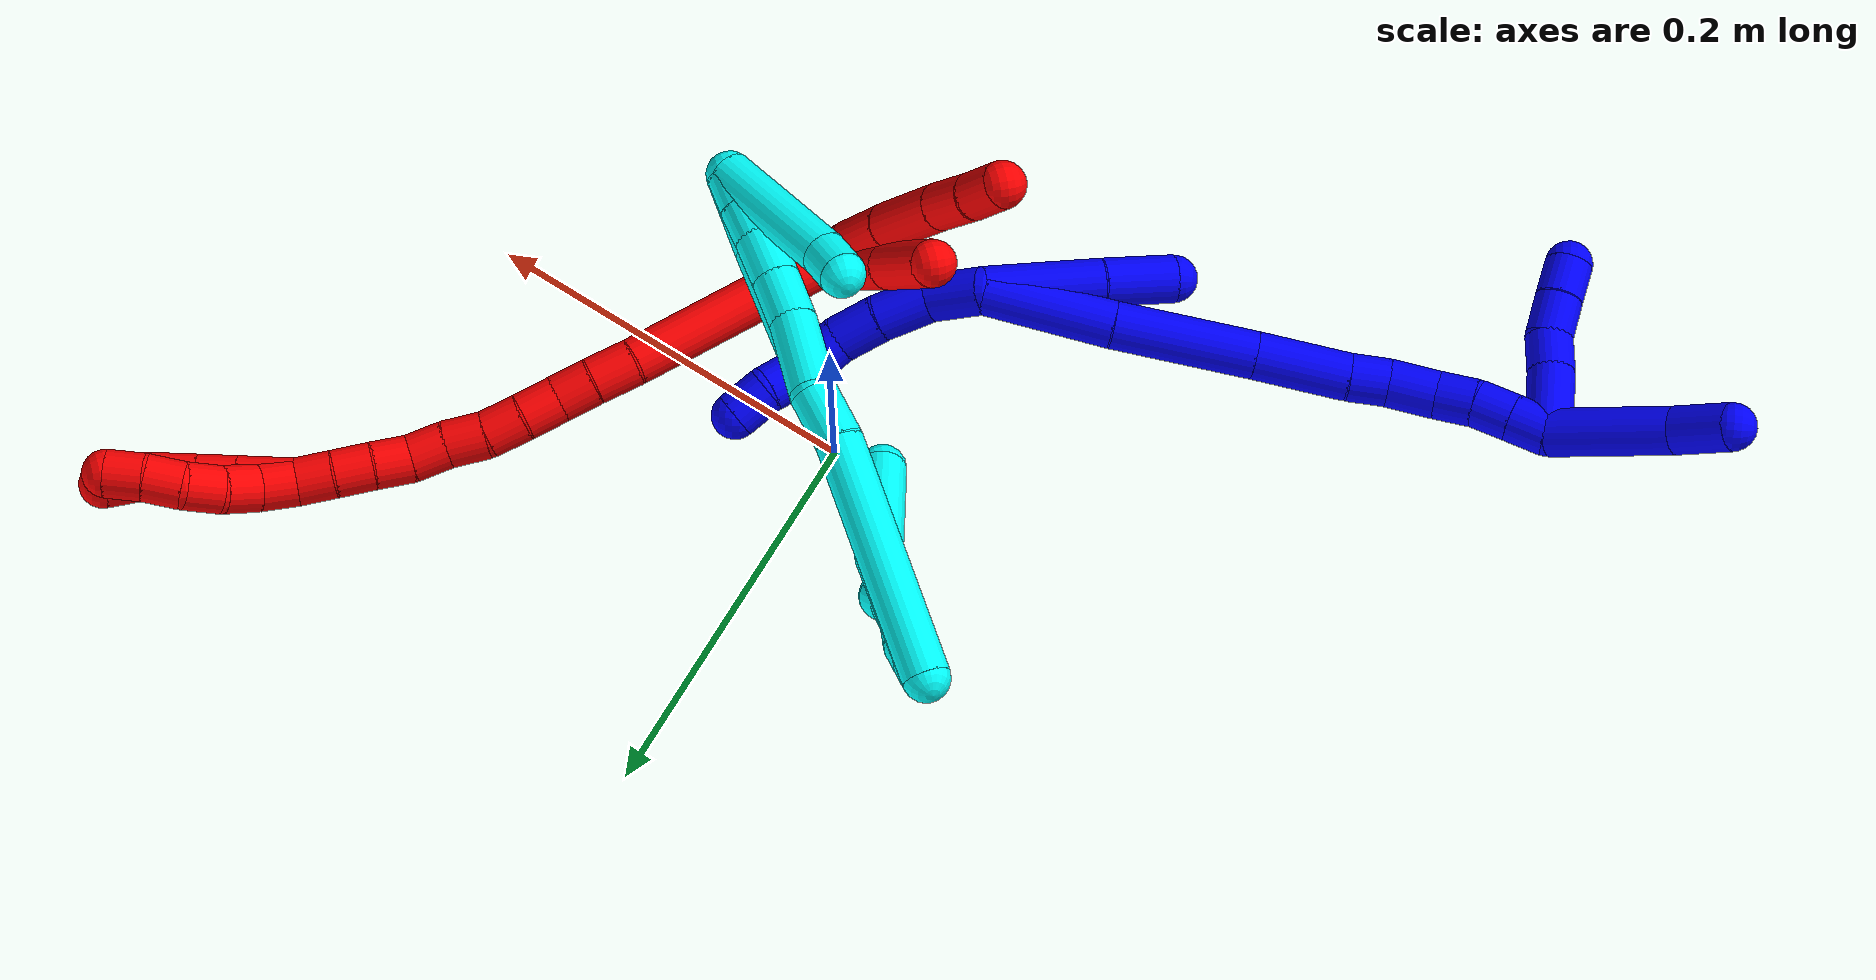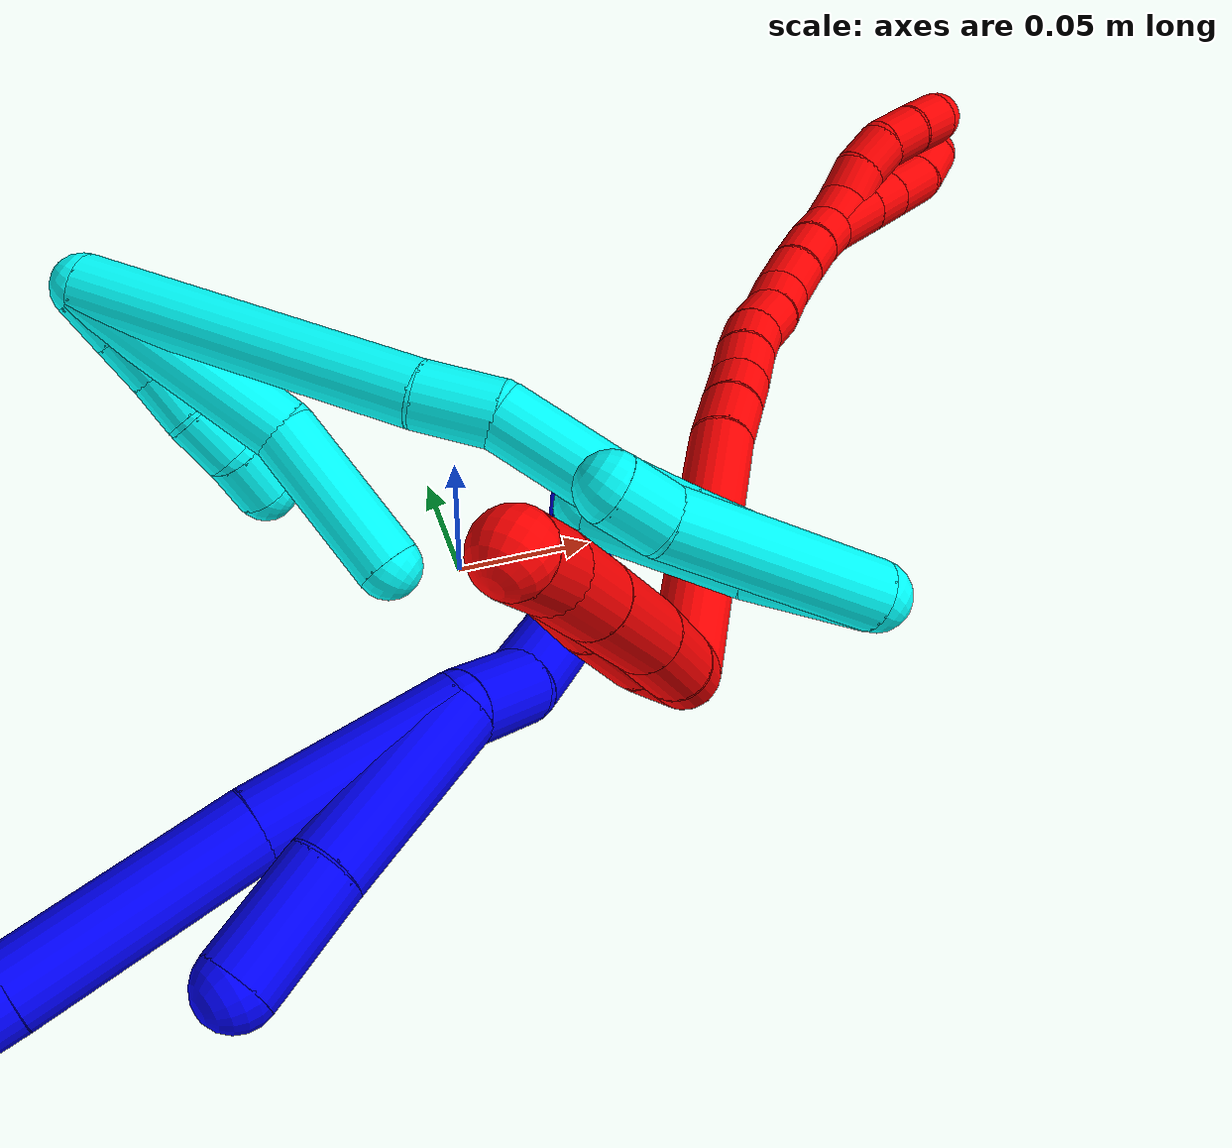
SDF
<sdf version="1.7">
 <world name="default">
  <plugin name="TubeGeneratorPlugin" filename="libtube_generator_plugin.so"/>
  <model name="photoneo_s_sensor">
   <static>1</static>
   <pose>0 0 2 1.57079 1.57079 3.14159</pose>
   <link name="link">
    <inertial><mass>0.1</mass></inertial>
    <sensor name="sensor" type="depth">
     <update_rate>30</update_rate>
     <camera>
      <horizontal_fov>1.22</horizontal_fov>
      <image><width>1920</width><height>1200</height><format>B8G8R8</format></image>
      <clip><near>0.1</near><far>4</far></clip>
      <depth_camera><output>points</output></depth_camera>
     </camera>
     <plugin name="camera_plugin" filename="libgazebo_ros_depth_camera.so">
      <baseline>0.2</baseline>
      <alwaysOn>1</alwaysOn>
      <updateRate>0.0</updateRate>
      <cameraName>camera_ir</cameraName>
      <imageTopicName>/camera/color/image_raw</imageTopicName>
      <cameraInfoTopicName>/camera/color/camera_info</cameraInfoTopicName>
      <depthImageTopicName>/camera/depth/image_raw</depthImageTopicName>
      <depthImageCameraInfoTopicName>/camera/depth/camera_info</depthImageCameraInfoTopicName>
      <pointCloudTopicName>/camera/depth/points</pointCloudTopicName>
      <frameName>fr_optical</frameName>
      <pointCloudCutoff>0.1</pointCloudCutoff>
      <pointCloudCutoffMax>2.0</pointCloudCutoffMax>
      <distortionK1>0</distortionK1>
      <distortionK2>0</distortionK2>
      <distortionK3>0</distortionK3>
      <distortionT1>0</distortionT1>
      <distortionT2>0</distortionT2>
      <CxPrime>0</CxPrime>
      <Cx>0</Cx>
      <Cy>0</Cy>
      <focalLength>0</focalLength>
      <hackBaseline>0</hackBaseline>
     </plugin>
    </sensor>
   </link>
  </model>
  <gravity>0 0 -9.8</gravity>
  <magnetic_field>6e-06 2.3e-05 -4.2e-05</magnetic_field>
  <atmosphere type="adiabatic"/>
  <physics name="default_physics" default="0" type="ode">
   <max_step_size>0.003</max_step_size>
   <real_time_factor>1</real_time_factor>
   <real_time_update_rate>1000</real_time_update_rate>
   <max_contacts>10000</max_contacts>
   <ode>
    <solver>
     <type>quick</type>
     <iters>100</iters>
     <sor>1.3</sor>
     <use_dynamic_moi_rescaling>0</use_dynamic_moi_rescaling>
    </solver>
    <constraints>
     <contact_max_correcting_vel>0</contact_max_correcting_vel>
     <contact_surface_layer>0.001</contact_surface_layer>
     <cfm>0</cfm>
     <erp>0.2</erp>
    </constraints>
   </ode>
  </physics>
  <scene><ambient>0.4 0.4 0.4 1</ambient><background>0.7 0.7 0.7 1</background><shadows>0</shadows></scene>
  <audio><device>default</device></audio>
  <spherical_coordinates>
   <surface_model>EARTH_WGS84</surface_model>
   <latitude_deg>0</latitude_deg>
   <longitude_deg>0</longitude_deg>
   <elevation>0</elevation>
   <heading_deg>0</heading_deg>
  </spherical_coordinates>
  <model name="bin">
   <static>1</static>
   <link name="bottom">
    <collision name="collision-bottom">
     <pose>0 0 -0.01 0 -0 0</pose>
     <geometry><box><size>0.8 0.6 0.02</size></box></geometry>
     <surface>
      <friction><ode><mu>100</mu><mu2>100</mu2></ode></friction>
      <contact><collide_bitmask>65535</collide_bitmask></contact>
     </surface>
    </collision>
   </link>
   <link name="west_wall">
    <collision name="collision-west_wall">
     <pose>-0.41 0 0.1 0 -0 0</pose>
     <geometry><box><size>0.02 0.6 0.2</size></box></geometry>
     <surface>
      <friction><ode><mu>100</mu><mu2>100</mu2></ode></friction>
      <contact><collide_bitmask>65535</collide_bitmask></contact>
     </surface>
    </collision>
   </link>
   <link name="east_wall">
    <collision name="collision-east_wall">
     <pose>0.41 0 0.1 0 -0 0</pose>
     <geometry><box><size>0.02 0.6 0.2</size></box></geometry>
     <surface>
      <friction><ode><mu>100</mu><mu2>100</mu2></ode></friction>
      <contact><collide_bitmask>65535</collide_bitmask></contact>
     </surface>
    </collision>
   </link>
   <link name="south_wall">
    <collision name="collision-south_wall">
     <pose>0 -0.31 0.1 0 -0 0</pose>
     <geometry><box><size>0.8 0.02 0.2</size></box></geometry>
     <surface>
      <friction><ode><mu>100</mu><mu2>100</mu2></ode></friction>
      <contact><collide_bitmask>65535</collide_bitmask></contact>
     </surface>
    </collision>
   </link>
   <link name="north_wall">
    <collision name="collision-north_wall">
     <pose>0 0.31 0.1 0 -0 0</pose>
     <geometry><box><size>0.8 0.02 0.2</size></box></geometry>
     <surface>
      <friction><ode><mu>100</mu><mu2>100</mu2></ode></friction>
      <contact><collide_bitmask>65535</collide_bitmask></contact>
     </surface>
    </collision>
   </link>
  </model>
  <model name="1">
   <static>0</static>
   <link name="1">
    <collision name="collision-cylinder-e_1_2_8">
     <pose>0.000251 0.005985 -0.013728 -2.73048 0.016747 -0.080279</pose>
     <geometry><cylinder><radius>0.0125</radius><length>0.029956</length></cylinder></geometry>
     <surface>
      <friction><ode><mu>1.16</mu><mu2>1.16</mu2><slip1>0</slip1><slip2>0</slip2></ode></friction>
      <contact><ode><kp>1e+06</kp><kd>1</kd><max_vel>0</max_vel><min_depth>0.001</min_depth></ode></contact>
     </surface>
    </collision>
    <visual name="visual-cylinder-e_1_2_8">
     <pose>0.000251 0.005985 -0.013728 -2.73048 0.016747 -0.080279</pose>
     <geometry><cylinder><radius>0.0125</radius><length>0.029956</length></cylinder></geometry>
     <material><ambient>0 0 1 1</ambient></material>
    </visual>
    <collision name="collision-cylinder-e_2_8_9">
     <pose>0.005371 0.016257 -0.040226 -2.81766 0.346872 -1.64047</pose>
     <geometry><cylinder><radius>0.0125</radius><length>0.028646</length></cylinder></geometry>
     <surface>
      <friction><ode><mu>1.16</mu><mu2>1.16</mu2><slip1>0</slip1><slip2>0</slip2></ode></friction>
      <contact><ode><kp>1e+06</kp><kd>1</kd><max_vel>0</max_vel><min_depth>0.001</min_depth></ode></contact>
     </surface>
    </collision>
    <visual name="visual-cylinder-e_2_8_9">
     <pose>0.005371 0.016257 -0.040226 -2.81766 0.346872 -1.64047</pose>
     <geometry><cylinder><radius>0.0125</radius><length>0.028646</length></cylinder></geometry>
     <material><ambient>0 0 1 1</ambient></material>
    </visual>
    <collision name="collision-cylinder-e_3_9_10">
     <pose>0.014945 0.02533 -0.063024 -2.69635 0.400554 -1.46202</pose>
     <geometry><cylinder><radius>0.0125</radius><length>0.024134</length></cylinder></geometry>
     <surface>
      <friction><ode><mu>1.16</mu><mu2>1.16</mu2><slip1>0</slip1><slip2>0</slip2></ode></friction>
      <contact><ode><kp>1e+06</kp><kd>1</kd><max_vel>0</max_vel><min_depth>0.001</min_depth></ode></contact>
     </surface>
    </collision>
    <visual name="visual-cylinder-e_3_9_10">
     <pose>0.014945 0.02533 -0.063024 -2.69635 0.400554 -1.46202</pose>
     <geometry><cylinder><radius>0.0125</radius><length>0.024134</length></cylinder></geometry>
     <material><ambient>0 0 1 1</ambient></material>
    </visual>
    <collision name="collision-cylinder-e_4_10_11">
     <pose>0.027176 0.033804 -0.08147 -2.72865 0.686084 -2.0808</pose>
     <geometry><cylinder><radius>0.0125</radius><length>0.023756</length></cylinder></geometry>
     <surface>
      <friction><ode><mu>1.16</mu><mu2>1.16</mu2><slip1>0</slip1><slip2>0</slip2></ode></friction>
      <contact><ode><kp>1e+06</kp><kd>1</kd><max_vel>0</max_vel><min_depth>0.001</min_depth></ode></contact>
     </surface>
    </collision>
    <visual name="visual-cylinder-e_4_10_11">
     <pose>0.027176 0.033804 -0.08147 -2.72865 0.686084 -2.0808</pose>
     <geometry><cylinder><radius>0.0125</radius><length>0.023756</length></cylinder></geometry>
     <material><ambient>0 0 1 1</ambient></material>
    </visual>
    <collision name="collision-cylinder-e_5_11_12">
     <pose>0.041672 0.037306 -0.098659 3.12035 0.671445 3.08073</pose>
     <geometry><cylinder><radius>0.0125</radius><length>0.022412</length></cylinder></geometry>
     <surface>
      <friction><ode><mu>1.16</mu><mu2>1.16</mu2><slip1>0</slip1><slip2>0</slip2></ode></friction>
      <contact><ode><kp>1e+06</kp><kd>1</kd><max_vel>0</max_vel><min_depth>0.001</min_depth></ode></contact>
     </surface>
    </collision>
    <visual name="visual-cylinder-e_5_11_12">
     <pose>0.041672 0.037306 -0.098659 3.12035 0.671445 3.08073</pose>
     <geometry><cylinder><radius>0.0125</radius><length>0.022412</length></cylinder></geometry>
     <material><ambient>0 0 1 1</ambient></material>
    </visual>
    <collision name="collision-cylinder-e_6_12_6">
     <pose>0.055455 0.040024 -0.114943 -2.77268 0.702025 -2.19912</pose>
     <geometry><cylinder><radius>0.0125</radius><length>0.021096</length></cylinder></geometry>
     <surface>
      <friction><ode><mu>1.16</mu><mu2>1.16</mu2><slip1>0</slip1><slip2>0</slip2></ode></friction>
      <contact><ode><kp>1e+06</kp><kd>1</kd><max_vel>0</max_vel><min_depth>0.001</min_depth></ode></contact>
     </surface>
    </collision>
    <visual name="visual-cylinder-e_6_12_6">
     <pose>0.055455 0.040024 -0.114943 -2.77268 0.702025 -2.19912</pose>
     <geometry><cylinder><radius>0.0125</radius><length>0.021096</length></cylinder></geometry>
     <material><ambient>0 0 1 1</ambient></material>
    </visual>
    <collision name="collision-cylinder-e_1_2_13">
     <pose>-0.007573 0.003924 0.029787 -0.130978 -0.24692 0.016276</pose>
     <geometry><cylinder><radius>0.0125</radius><length>0.061968</length></cylinder></geometry>
     <surface>
      <friction><ode><mu>1.16</mu><mu2>1.16</mu2><slip1>0</slip1><slip2>0</slip2></ode></friction>
      <contact><ode><kp>1e+06</kp><kd>1</kd><max_vel>0</max_vel><min_depth>0.001</min_depth></ode></contact>
     </surface>
    </collision>
    <visual name="visual-cylinder-e_1_2_13">
     <pose>-0.007573 0.003924 0.029787 -0.130978 -0.24692 0.016276</pose>
     <geometry><cylinder><radius>0.0125</radius><length>0.061968</length></cylinder></geometry>
     <material><ambient>0 0 1 1</ambient></material>
    </visual>
    <collision name="collision-cylinder-e_2_13_5">
     <pose>-0.020098 0.011721 0.07752 -0.212581 -0.26342 0.028267</pose>
     <geometry><cylinder><radius>0.0125</radius><length>0.038032</length></cylinder></geometry>
     <surface>
      <friction><ode><mu>1.16</mu><mu2>1.16</mu2><slip1>0</slip1><slip2>0</slip2></ode></friction>
      <contact><ode><kp>1e+06</kp><kd>1</kd><max_vel>0</max_vel><min_depth>0.001</min_depth></ode></contact>
     </surface>
    </collision>
    <visual name="visual-cylinder-e_2_13_5">
     <pose>-0.020098 0.011721 0.07752 -0.212581 -0.26342 0.028267</pose>
     <geometry><cylinder><radius>0.0125</radius><length>0.038032</length></cylinder></geometry>
     <material><ambient>0 0 1 1</ambient></material>
    </visual>
    <collision name="collision-cylinder-e_1_2_14">
     <pose>0.003837 0.005146 0.033577 -0.152076 0.11249 -0.008579</pose>
     <geometry><cylinder><radius>0.0125</radius><length>0.06837</length></cylinder></geometry>
     <surface>
      <friction><ode><mu>1.16</mu><mu2>1.16</mu2><slip1>0</slip1><slip2>0</slip2></ode></friction>
      <contact><ode><kp>1e+06</kp><kd>1</kd><max_vel>0</max_vel><min_depth>0.001</min_depth></ode></contact>
     </surface>
    </collision>
    <visual name="visual-cylinder-e_1_2_14">
     <pose>0.003837 0.005146 0.033577 -0.152076 0.11249 -0.008579</pose>
     <geometry><cylinder><radius>0.0125</radius><length>0.06837</length></cylinder></geometry>
     <material><ambient>0 0 1 1</ambient></material>
    </visual>
    <collision name="collision-cylinder-e_2_14_15">
     <pose>0.009574 0.016532 0.103952 -0.167981 0.050833 -0.00428</pose>
     <geometry><cylinder><radius>0.0125</radius><length>0.074744</length></cylinder></geometry>
     <surface>
      <friction><ode><mu>1.16</mu><mu2>1.16</mu2><slip1>0</slip1><slip2>0</slip2></ode></friction>
      <contact><ode><kp>1e+06</kp><kd>1</kd><max_vel>0</max_vel><min_depth>0.001</min_depth></ode></contact>
     </surface>
    </collision>
    <visual name="visual-cylinder-e_2_14_15">
     <pose>0.009574 0.016532 0.103952 -0.167981 0.050833 -0.00428</pose>
     <geometry><cylinder><radius>0.0125</radius><length>0.074744</length></cylinder></geometry>
     <material><ambient>0 0 1 1</ambient></material>
    </visual>
    <collision name="collision-cylinder-e_3_15_16">
     <pose>0.013291 0.026737 0.165007 -0.161995 0.073857 -0.005998</pose>
     <geometry><cylinder><radius>0.0125</radius><length>0.049291</length></cylinder></geometry>
     <surface>
      <friction><ode><mu>1.16</mu><mu2>1.16</mu2><slip1>0</slip1><slip2>0</slip2></ode></friction>
      <contact><ode><kp>1e+06</kp><kd>1</kd><max_vel>0</max_vel><min_depth>0.001</min_depth></ode></contact>
     </surface>
    </collision>
    <visual name="visual-cylinder-e_3_15_16">
     <pose>0.013291 0.026737 0.165007 -0.161995 0.073857 -0.005998</pose>
     <geometry><cylinder><radius>0.0125</radius><length>0.049291</length></cylinder></geometry>
     <material><ambient>0 0 1 1</ambient></material>
    </visual>
    <collision name="collision-cylinder-e_4_16_17">
     <pose>0.01496 0.03215 0.199566 -0.139717 -0.014406 0.001008</pose>
     <geometry><cylinder><radius>0.0125</radius><length>0.020809</length></cylinder></geometry>
     <surface>
      <friction><ode><mu>1.16</mu><mu2>1.16</mu2><slip1>0</slip1><slip2>0</slip2></ode></friction>
      <contact><ode><kp>1e+06</kp><kd>1</kd><max_vel>0</max_vel><min_depth>0.001</min_depth></ode></contact>
     </surface>
    </collision>
    <visual name="visual-cylinder-e_4_16_17">
     <pose>0.01496 0.03215 0.199566 -0.139717 -0.014406 0.001008</pose>
     <geometry><cylinder><radius>0.0125</radius><length>0.020809</length></cylinder></geometry>
     <material><ambient>0 0 1 1</ambient></material>
    </visual>
    <collision name="collision-cylinder-e_5_17_18">
     <pose>0.016768 0.034261 0.222729 -0.051511 0.150867 -0.003894</pose>
     <geometry><cylinder><radius>0.0125</radius><length>0.026052</length></cylinder></geometry>
     <surface>
      <friction><ode><mu>1.16</mu><mu2>1.16</mu2><slip1>0</slip1><slip2>0</slip2></ode></friction>
      <contact><ode><kp>1e+06</kp><kd>1</kd><max_vel>0</max_vel><min_depth>0.001</min_depth></ode></contact>
     </surface>
    </collision>
    <visual name="visual-cylinder-e_5_17_18">
     <pose>0.016768 0.034261 0.222729 -0.051511 0.150867 -0.003894</pose>
     <geometry><cylinder><radius>0.0125</radius><length>0.026052</length></cylinder></geometry>
     <material><ambient>0 0 1 1</ambient></material>
    </visual>
    <collision name="collision-cylinder-e_6_18_19">
     <pose>0.020721 0.033824 0.245626 0.109167 0.195089 0.010693</pose>
     <geometry><cylinder><radius>0.0125</radius><length>0.020585</length></cylinder></geometry>
     <surface>
      <friction><ode><mu>1.16</mu><mu2>1.16</mu2><slip1>0</slip1><slip2>0</slip2></ode></friction>
      <contact><ode><kp>1e+06</kp><kd>1</kd><max_vel>0</max_vel><min_depth>0.001</min_depth></ode></contact>
     </surface>
    </collision>
    <visual name="visual-cylinder-e_6_18_19">
     <pose>0.020721 0.033824 0.245626 0.109167 0.195089 0.010693</pose>
     <geometry><cylinder><radius>0.0125</radius><length>0.020585</length></cylinder></geometry>
     <material><ambient>0 0 1 1</ambient></material>
    </visual>
    <collision name="collision-cylinder-e_7_19_20">
     <pose>0.026032 0.032601 0.265102 0.013029 0.33785 0.002222</pose>
     <geometry><cylinder><radius>0.0125</radius><length>0.020009</length></cylinder></geometry>
     <surface>
      <friction><ode><mu>1.16</mu><mu2>1.16</mu2><slip1>0</slip1><slip2>0</slip2></ode></friction>
      <contact><ode><kp>1e+06</kp><kd>1</kd><max_vel>0</max_vel><min_depth>0.001</min_depth></ode></contact>
     </surface>
    </collision>
    <visual name="visual-cylinder-e_7_19_20">
     <pose>0.026032 0.032601 0.265102 0.013029 0.33785 0.002222</pose>
     <geometry><cylinder><radius>0.0125</radius><length>0.020009</length></cylinder></geometry>
     <material><ambient>0 0 1 1</ambient></material>
    </visual>
    <collision name="collision-cylinder-e_8_20_1">
     <pose>0.032697 0.032463 0.284037 0.001601 0.339026 0.000274</pose>
     <geometry><cylinder><radius>0.0125</radius><length>0.02014</length></cylinder></geometry>
     <surface>
      <friction><ode><mu>1.16</mu><mu2>1.16</mu2><slip1>0</slip1><slip2>0</slip2></ode></friction>
      <contact><ode><kp>1e+06</kp><kd>1</kd><max_vel>0</max_vel><min_depth>0.001</min_depth></ode></contact>
     </surface>
    </collision>
    <visual name="visual-cylinder-e_8_20_1">
     <pose>0.032697 0.032463 0.284037 0.001601 0.339026 0.000274</pose>
     <geometry><cylinder><radius>0.0125</radius><length>0.02014</length></cylinder></geometry>
     <material><ambient>0 0 1 1</ambient></material>
    </visual>
    <collision name="collision-cylinder-e_1_1_21">
     <pose>0.038251 0.021003 0.324799 0.350923 0.066121 0.011726</pose>
     <geometry><cylinder><radius>0.0125</radius><length>0.066735</length></cylinder></geometry>
     <surface>
      <friction><ode><mu>1.16</mu><mu2>1.16</mu2><slip1>0</slip1><slip2>0</slip2></ode></friction>
      <contact><ode><kp>1e+06</kp><kd>1</kd><max_vel>0</max_vel><min_depth>0.001</min_depth></ode></contact>
     </surface>
    </collision>
    <visual name="visual-cylinder-e_1_1_21">
     <pose>0.038251 0.021003 0.324799 0.350923 0.066121 0.011726</pose>
     <geometry><cylinder><radius>0.0125</radius><length>0.066735</length></cylinder></geometry>
     <material><ambient>0 0 1 1</ambient></material>
    </visual>
    <collision name="collision-cylinder-e_2_21_4">
     <pose>0.042788 0.000514 0.369828 0.581327 0.140717 0.042157</pose>
     <geometry><cylinder><radius>0.0125</radius><length>0.033265</length></cylinder></geometry>
     <surface>
      <friction><ode><mu>1.16</mu><mu2>1.16</mu2><slip1>0</slip1><slip2>0</slip2></ode></friction>
      <contact><ode><kp>1e+06</kp><kd>1</kd><max_vel>0</max_vel><min_depth>0.001</min_depth></ode></contact>
     </surface>
    </collision>
    <visual name="visual-cylinder-e_2_21_4">
     <pose>0.042788 0.000514 0.369828 0.581327 0.140717 0.042157</pose>
     <geometry><cylinder><radius>0.0125</radius><length>0.033265</length></cylinder></geometry>
     <material><ambient>0 0 1 1</ambient></material>
    </visual>
    <collision name="collision-cylinder-e_1_1_22">
     <pose>0.017833 0.034369 0.293251 -1.71707 -1.46461 1.61119</pose>
     <geometry><cylinder><radius>0.0125</radius><length>0.036633</length></cylinder></geometry>
     <surface>
      <friction><ode><mu>1.16</mu><mu2>1.16</mu2><slip1>0</slip1><slip2>0</slip2></ode></friction>
      <contact><ode><kp>1e+06</kp><kd>1</kd><max_vel>0</max_vel><min_depth>0.001</min_depth></ode></contact>
     </surface>
    </collision>
    <visual name="visual-cylinder-e_1_1_22">
     <pose>0.017833 0.034369 0.293251 -1.71707 -1.46461 1.61119</pose>
     <geometry><cylinder><radius>0.0125</radius><length>0.036633</length></cylinder></geometry>
     <material><ambient>0 0 1 1</ambient></material>
    </visual>
    <collision name="collision-cylinder-e_2_22_23">
     <pose>-0.010673 0.036167 0.291725 3.04366 -1.45005 -3.03109</pose>
     <geometry><cylinder><radius>0.0125</radius><length>0.020735</length></cylinder></geometry>
     <surface>
      <friction><ode><mu>1.16</mu><mu2>1.16</mu2><slip1>0</slip1><slip2>0</slip2></ode></friction>
      <contact><ode><kp>1e+06</kp><kd>1</kd><max_vel>0</max_vel><min_depth>0.001</min_depth></ode></contact>
     </surface>
    </collision>
    <visual name="visual-cylinder-e_2_22_23">
     <pose>-0.010673 0.036167 0.291725 3.04366 -1.45005 -3.03109</pose>
     <geometry><cylinder><radius>0.0125</radius><length>0.020735</length></cylinder></geometry>
     <material><ambient>0 0 1 1</ambient></material>
    </visual>
    <collision name="collision-cylinder-e_3_23_24">
     <pose>-0.031662 0.034669 0.292285 0.651864 -1.36186 -0.534569</pose>
     <geometry><cylinder><radius>0.0125</radius><length>0.021869</length></cylinder></geometry>
     <surface>
      <friction><ode><mu>1.16</mu><mu2>1.16</mu2><slip1>0</slip1><slip2>0</slip2></ode></friction>
      <contact><ode><kp>1e+06</kp><kd>1</kd><max_vel>0</max_vel><min_depth>0.001</min_depth></ode></contact>
     </surface>
    </collision>
    <visual name="visual-cylinder-e_3_23_24">
     <pose>-0.031662 0.034669 0.292285 0.651864 -1.36186 -0.534569</pose>
     <geometry><cylinder><radius>0.0125</radius><length>0.021869</length></cylinder></geometry>
     <material><ambient>0 0 1 1</ambient></material>
    </visual>
    <collision name="collision-cylinder-e_4_24_3">
     <pose>-0.052536 0.032595 0.296014 0.347806 -1.3722 -0.285731</pose>
     <geometry><cylinder><radius>0.0125</radius><length>0.020763</length></cylinder></geometry>
     <surface>
      <friction><ode><mu>1.16</mu><mu2>1.16</mu2><slip1>0</slip1><slip2>0</slip2></ode></friction>
      <contact><ode><kp>1e+06</kp><kd>1</kd><max_vel>0</max_vel><min_depth>0.001</min_depth></ode></contact>
     </surface>
    </collision>
    <visual name="visual-cylinder-e_4_24_3">
     <pose>-0.052536 0.032595 0.296014 0.347806 -1.3722 -0.285731</pose>
     <geometry><cylinder><radius>0.0125</radius><length>0.020763</length></cylinder></geometry>
     <material><ambient>0 0 1 1</ambient></material>
    </visual>
    <collision name="collision-sphere-3">
     <pose>-0.062713 0.031897 0.297939 0 -0 0</pose>
     <geometry><sphere><radius>0.0125</radius></sphere></geometry>
     <surface>
      <friction><ode><mu>1.16</mu><mu2>1.16</mu2><slip1>0</slip1><slip2>0</slip2></ode></friction>
      <contact><ode><kp>1e+06</kp><kd>1</kd><max_vel>0</max_vel><min_depth>0.001</min_depth></ode></contact>
     </surface>
    </collision>
    <visual name="visual-sphere-3">
     <pose>-0.062713 0.031897 0.297939 0 -0 0</pose>
     <geometry><sphere><radius>0.0125</radius></sphere></geometry>
     <material><ambient>0 0 1 1</ambient></material>
    </visual>
    <collision name="collision-sphere-24">
     <pose>-0.042358 0.033293 0.294088 0 -0 0</pose>
     <geometry><sphere><radius>0.0125</radius></sphere></geometry>
     <surface>
      <friction><ode><mu>1.16</mu><mu2>1.16</mu2><slip1>0</slip1><slip2>0</slip2></ode></friction>
      <contact><ode><kp>1e+06</kp><kd>1</kd><max_vel>0</max_vel><min_depth>0.001</min_depth></ode></contact>
     </surface>
    </collision>
    <visual name="visual-sphere-24">
     <pose>-0.042358 0.033293 0.294088 0 -0 0</pose>
     <geometry><sphere><radius>0.0125</radius></sphere></geometry>
     <material><ambient>0 0 1 1</ambient></material>
    </visual>
    <collision name="collision-sphere-23">
     <pose>-0.020965 0.036045 0.290482 0 -0 0</pose>
     <geometry><sphere><radius>0.0125</radius></sphere></geometry>
     <surface>
      <friction><ode><mu>1.16</mu><mu2>1.16</mu2><slip1>0</slip1><slip2>0</slip2></ode></friction>
      <contact><ode><kp>1e+06</kp><kd>1</kd><max_vel>0</max_vel><min_depth>0.001</min_depth></ode></contact>
     </surface>
    </collision>
    <visual name="visual-sphere-23">
     <pose>-0.020965 0.036045 0.290482 0 -0 0</pose>
     <geometry><sphere><radius>0.0125</radius></sphere></geometry>
     <material><ambient>0 0 1 1</ambient></material>
    </visual>
    <collision name="collision-sphere-22">
     <pose>-0.000381 0.036289 0.292968 0 -0 0</pose>
     <geometry><sphere><radius>0.0125</radius></sphere></geometry>
     <surface>
      <friction><ode><mu>1.16</mu><mu2>1.16</mu2><slip1>0</slip1><slip2>0</slip2></ode></friction>
      <contact><ode><kp>1e+06</kp><kd>1</kd><max_vel>0</max_vel><min_depth>0.001</min_depth></ode></contact>
     </surface>
    </collision>
    <visual name="visual-sphere-22">
     <pose>-0.000381 0.036289 0.292968 0 -0 0</pose>
     <geometry><sphere><radius>0.0125</radius></sphere></geometry>
     <material><ambient>0 0 1 1</ambient></material>
    </visual>
    <collision name="collision-sphere-4">
     <pose>0.045121 -0.008529 0.383591 0 -0 0</pose>
     <geometry><sphere><radius>0.0125</radius></sphere></geometry>
     <surface>
      <friction><ode><mu>1.16</mu><mu2>1.16</mu2><slip1>0</slip1><slip2>0</slip2></ode></friction>
      <contact><ode><kp>1e+06</kp><kd>1</kd><max_vel>0</max_vel><min_depth>0.001</min_depth></ode></contact>
     </surface>
    </collision>
    <visual name="visual-sphere-4">
     <pose>0.045121 -0.008529 0.383591 0 -0 0</pose>
     <geometry><sphere><radius>0.0125</radius></sphere></geometry>
     <material><ambient>0 0 1 1</ambient></material>
    </visual>
    <collision name="collision-sphere-21">
     <pose>0.040455 0.009557 0.356064 0 -0 0</pose>
     <geometry><sphere><radius>0.0125</radius></sphere></geometry>
     <surface>
      <friction><ode><mu>1.16</mu><mu2>1.16</mu2><slip1>0</slip1><slip2>0</slip2></ode></friction>
      <contact><ode><kp>1e+06</kp><kd>1</kd><max_vel>0</max_vel><min_depth>0.001</min_depth></ode></contact>
     </surface>
    </collision>
    <visual name="visual-sphere-21">
     <pose>0.040455 0.009557 0.356064 0 -0 0</pose>
     <geometry><sphere><radius>0.0125</radius></sphere></geometry>
     <material><ambient>0 0 1 1</ambient></material>
    </visual>
    <collision name="collision-sphere-1">
     <pose>0.036046 0.032448 0.293534 0 -0 0</pose>
     <geometry><sphere><radius>0.0125</radius></sphere></geometry>
     <surface>
      <friction><ode><mu>1.16</mu><mu2>1.16</mu2><slip1>0</slip1><slip2>0</slip2></ode></friction>
      <contact><ode><kp>1e+06</kp><kd>1</kd><max_vel>0</max_vel><min_depth>0.001</min_depth></ode></contact>
     </surface>
    </collision>
    <visual name="visual-sphere-1">
     <pose>0.036046 0.032448 0.293534 0 -0 0</pose>
     <geometry><sphere><radius>0.0125</radius></sphere></geometry>
     <material><ambient>0 0 1 1</ambient></material>
    </visual>
    <collision name="collision-sphere-12">
     <pose>0.048643 0.03712 -0.107431 0 -0 0</pose>
     <geometry><sphere><radius>0.0125</radius></sphere></geometry>
     <surface>
      <friction><ode><mu>1.16</mu><mu2>1.16</mu2><slip1>0</slip1><slip2>0</slip2></ode></friction>
      <contact><ode><kp>1e+06</kp><kd>1</kd><max_vel>0</max_vel><min_depth>0.001</min_depth></ode></contact>
     </surface>
    </collision>
    <visual name="visual-sphere-12">
     <pose>0.048643 0.03712 -0.107431 0 -0 0</pose>
     <geometry><sphere><radius>0.0125</radius></sphere></geometry>
     <material><ambient>0 0 1 1</ambient></material>
    </visual>
    <collision name="collision-sphere-11">
     <pose>0.0347 0.037492 -0.089888 0 -0 0</pose>
     <geometry><sphere><radius>0.0125</radius></sphere></geometry>
     <surface>
      <friction><ode><mu>1.16</mu><mu2>1.16</mu2><slip1>0</slip1><slip2>0</slip2></ode></friction>
      <contact><ode><kp>1e+06</kp><kd>1</kd><max_vel>0</max_vel><min_depth>0.001</min_depth></ode></contact>
     </surface>
    </collision>
    <visual name="visual-sphere-11">
     <pose>0.0347 0.037492 -0.089888 0 -0 0</pose>
     <geometry><sphere><radius>0.0125</radius></sphere></geometry>
     <material><ambient>0 0 1 1</ambient></material>
    </visual>
    <collision name="collision-sphere-10">
     <pose>0.019651 0.030116 -0.073052 0 -0 0</pose>
     <geometry><sphere><radius>0.0125</radius></sphere></geometry>
     <surface>
      <friction><ode><mu>1.16</mu><mu2>1.16</mu2><slip1>0</slip1><slip2>0</slip2></ode></friction>
      <contact><ode><kp>1e+06</kp><kd>1</kd><max_vel>0</max_vel><min_depth>0.001</min_depth></ode></contact>
     </surface>
    </collision>
    <visual name="visual-sphere-10">
     <pose>0.019651 0.030116 -0.073052 0 -0 0</pose>
     <geometry><sphere><radius>0.0125</radius></sphere></geometry>
     <material><ambient>0 0 1 1</ambient></material>
    </visual>
    <collision name="collision-sphere-9">
     <pose>0.01024 0.020545 -0.052995 0 -0 0</pose>
     <geometry><sphere><radius>0.0125</radius></sphere></geometry>
     <surface>
      <friction><ode><mu>1.16</mu><mu2>1.16</mu2><slip1>0</slip1><slip2>0</slip2></ode></friction>
      <contact><ode><kp>1e+06</kp><kd>1</kd><max_vel>0</max_vel><min_depth>0.001</min_depth></ode></contact>
     </surface>
    </collision>
    <visual name="visual-sphere-9">
     <pose>0.01024 0.020545 -0.052995 0 -0 0</pose>
     <geometry><sphere><radius>0.0125</radius></sphere></geometry>
     <material><ambient>0 0 1 1</ambient></material>
    </visual>
    <collision name="collision-sphere-2">
     <geometry><sphere><radius>0.0125</radius></sphere></geometry>
     <surface>
      <friction><ode><mu>1.16</mu><mu2>1.16</mu2><slip1>0</slip1><slip2>0</slip2></ode></friction>
      <contact><ode><kp>1e+06</kp><kd>1</kd><max_vel>0</max_vel><min_depth>0.001</min_depth></ode></contact>
     </surface>
    </collision>
    <visual name="visual-sphere-2">
     <geometry><sphere><radius>0.0125</radius></sphere></geometry>
     <material><ambient>0 0 1 1</ambient></material>
    </visual>
    <collision name="collision-sphere-19">
     <pose>0.022716 0.032724 0.255663 0 -0 0</pose>
     <geometry><sphere><radius>0.0125</radius></sphere></geometry>
     <surface>
      <friction><ode><mu>1.16</mu><mu2>1.16</mu2><slip1>0</slip1><slip2>0</slip2></ode></friction>
      <contact><ode><kp>1e+06</kp><kd>1</kd><max_vel>0</max_vel><min_depth>0.001</min_depth></ode></contact>
     </surface>
    </collision>
    <visual name="visual-sphere-19">
     <pose>0.022716 0.032724 0.255663 0 -0 0</pose>
     <geometry><sphere><radius>0.0125</radius></sphere></geometry>
     <material><ambient>0 0 1 1</ambient></material>
    </visual>
    <collision name="collision-sphere-8">
     <pose>0.000502 0.01197 -0.027456 0 -0 0</pose>
     <geometry><sphere><radius>0.0125</radius></sphere></geometry>
     <surface>
      <friction><ode><mu>1.16</mu><mu2>1.16</mu2><slip1>0</slip1><slip2>0</slip2></ode></friction>
      <contact><ode><kp>1e+06</kp><kd>1</kd><max_vel>0</max_vel><min_depth>0.001</min_depth></ode></contact>
     </surface>
    </collision>
    <visual name="visual-sphere-8">
     <pose>0.000502 0.01197 -0.027456 0 -0 0</pose>
     <geometry><sphere><radius>0.0125</radius></sphere></geometry>
     <material><ambient>0 0 1 1</ambient></material>
    </visual>
    <collision name="collision-sphere-6">
     <pose>0.062266 0.042928 -0.122454 0 -0 0</pose>
     <geometry><sphere><radius>0.0125</radius></sphere></geometry>
     <surface>
      <friction><ode><mu>1.16</mu><mu2>1.16</mu2><slip1>0</slip1><slip2>0</slip2></ode></friction>
      <contact><ode><kp>1e+06</kp><kd>1</kd><max_vel>0</max_vel><min_depth>0.001</min_depth></ode></contact>
     </surface>
    </collision>
    <visual name="visual-sphere-6">
     <pose>0.062266 0.042928 -0.122454 0 -0 0</pose>
     <geometry><sphere><radius>0.0125</radius></sphere></geometry>
     <material><ambient>0 0 1 1</ambient></material>
    </visual>
    <collision name="collision-sphere-13">
     <pose>-0.015146 0.007848 0.059574 0 -0 0</pose>
     <geometry><sphere><radius>0.0125</radius></sphere></geometry>
     <surface>
      <friction><ode><mu>1.16</mu><mu2>1.16</mu2><slip1>0</slip1><slip2>0</slip2></ode></friction>
      <contact><ode><kp>1e+06</kp><kd>1</kd><max_vel>0</max_vel><min_depth>0.001</min_depth></ode></contact>
     </surface>
    </collision>
    <visual name="visual-sphere-13">
     <pose>-0.015146 0.007848 0.059574 0 -0 0</pose>
     <geometry><sphere><radius>0.0125</radius></sphere></geometry>
     <material><ambient>0 0 1 1</ambient></material>
    </visual>
    <collision name="collision-sphere-5">
     <pose>-0.025049 0.015595 0.095467 0 -0 0</pose>
     <geometry><sphere><radius>0.0125</radius></sphere></geometry>
     <surface>
      <friction><ode><mu>1.16</mu><mu2>1.16</mu2><slip1>0</slip1><slip2>0</slip2></ode></friction>
      <contact><ode><kp>1e+06</kp><kd>1</kd><max_vel>0</max_vel><min_depth>0.001</min_depth></ode></contact>
     </surface>
    </collision>
    <visual name="visual-sphere-5">
     <pose>-0.025049 0.015595 0.095467 0 -0 0</pose>
     <geometry><sphere><radius>0.0125</radius></sphere></geometry>
     <material><ambient>0 0 1 1</ambient></material>
    </visual>
    <collision name="collision-sphere-14">
     <pose>0.007675 0.010292 0.067153 0 -0 0</pose>
     <geometry><sphere><radius>0.0125</radius></sphere></geometry>
     <surface>
      <friction><ode><mu>1.16</mu><mu2>1.16</mu2><slip1>0</slip1><slip2>0</slip2></ode></friction>
      <contact><ode><kp>1e+06</kp><kd>1</kd><max_vel>0</max_vel><min_depth>0.001</min_depth></ode></contact>
     </surface>
    </collision>
    <visual name="visual-sphere-14">
     <pose>0.007675 0.010292 0.067153 0 -0 0</pose>
     <geometry><sphere><radius>0.0125</radius></sphere></geometry>
     <material><ambient>0 0 1 1</ambient></material>
    </visual>
    <collision name="collision-sphere-15">
     <pose>0.011473 0.022772 0.14075 0 -0 0</pose>
     <geometry><sphere><radius>0.0125</radius></sphere></geometry>
     <surface>
      <friction><ode><mu>1.16</mu><mu2>1.16</mu2><slip1>0</slip1><slip2>0</slip2></ode></friction>
      <contact><ode><kp>1e+06</kp><kd>1</kd><max_vel>0</max_vel><min_depth>0.001</min_depth></ode></contact>
     </surface>
    </collision>
    <visual name="visual-sphere-15">
     <pose>0.011473 0.022772 0.14075 0 -0 0</pose>
     <geometry><sphere><radius>0.0125</radius></sphere></geometry>
     <material><ambient>0 0 1 1</ambient></material>
    </visual>
    <collision name="collision-sphere-16">
     <pose>0.01511 0.030701 0.189264 0 -0 0</pose>
     <geometry><sphere><radius>0.0125</radius></sphere></geometry>
     <surface>
      <friction><ode><mu>1.16</mu><mu2>1.16</mu2><slip1>0</slip1><slip2>0</slip2></ode></friction>
      <contact><ode><kp>1e+06</kp><kd>1</kd><max_vel>0</max_vel><min_depth>0.001</min_depth></ode></contact>
     </surface>
    </collision>
    <visual name="visual-sphere-16">
     <pose>0.01511 0.030701 0.189264 0 -0 0</pose>
     <geometry><sphere><radius>0.0125</radius></sphere></geometry>
     <material><ambient>0 0 1 1</ambient></material>
    </visual>
    <collision name="collision-sphere-17">
     <pose>0.01481 0.033598 0.209868 0 -0 0</pose>
     <geometry><sphere><radius>0.0125</radius></sphere></geometry>
     <surface>
      <friction><ode><mu>1.16</mu><mu2>1.16</mu2><slip1>0</slip1><slip2>0</slip2></ode></friction>
      <contact><ode><kp>1e+06</kp><kd>1</kd><max_vel>0</max_vel><min_depth>0.001</min_depth></ode></contact>
     </surface>
    </collision>
    <visual name="visual-sphere-17">
     <pose>0.01481 0.033598 0.209868 0 -0 0</pose>
     <geometry><sphere><radius>0.0125</radius></sphere></geometry>
     <material><ambient>0 0 1 1</ambient></material>
    </visual>
    <collision name="collision-sphere-18">
     <pose>0.018725 0.034925 0.235589 0 -0 0</pose>
     <geometry><sphere><radius>0.0125</radius></sphere></geometry>
     <surface>
      <friction><ode><mu>1.16</mu><mu2>1.16</mu2><slip1>0</slip1><slip2>0</slip2></ode></friction>
      <contact><ode><kp>1e+06</kp><kd>1</kd><max_vel>0</max_vel><min_depth>0.001</min_depth></ode></contact>
     </surface>
    </collision>
    <visual name="visual-sphere-18">
     <pose>0.018725 0.034925 0.235589 0 -0 0</pose>
     <geometry><sphere><radius>0.0125</radius></sphere></geometry>
     <material><ambient>0 0 1 1</ambient></material>
    </visual>
    <collision name="collision-sphere-20">
     <pose>0.029348 0.032478 0.27454 0 -0 0</pose>
     <geometry><sphere><radius>0.0125</radius></sphere></geometry>
     <surface>
      <friction><ode><mu>1.16</mu><mu2>1.16</mu2><slip1>0</slip1><slip2>0</slip2></ode></friction>
      <contact><ode><kp>1e+06</kp><kd>1</kd><max_vel>0</max_vel><min_depth>0.001</min_depth></ode></contact>
     </surface>
    </collision>
    <visual name="visual-sphere-20">
     <pose>0.029348 0.032478 0.27454 0 -0 0</pose>
     <geometry><sphere><radius>0.0125</radius></sphere></geometry>
     <material><ambient>0 0 1 1</ambient></material>
    </visual>
    <inertial>
     <pose>0.011533 0.021014 0.136908 0 -0 0</pose>
     <mass>0.75</mass>
     <inertia><ixx>0.000139</ixx><ixy>0</ixy><ixz>0</ixz><iyy>0.000153</iyy><iyz>0</iyz><izz>2e-05</izz></inertia>
    </inertial>
   </link>
   <pose>-0.025606 -0.10382 0.04414 -1.52694 -0.231138 2.01584</pose>
  </model>
  <model name="2">
   <static>0</static>
   <link name="2">
    <collision name="collision-cylinder-e_1_2_8">
     <pose>-0.008163 -0.005109 -0.004757 2.32048 -0.863274 -1.62729</pose>
     <geometry><cylinder><radius>0.0125</radius><length>0.021482</length></cylinder></geometry>
     <surface>
      <friction><ode><mu>1.16</mu><mu2>1.16</mu2><slip1>0</slip1><slip2>0</slip2></ode></friction>
      <contact><ode><kp>1e+06</kp><kd>1</kd><max_vel>0</max_vel><min_depth>0.001</min_depth></ode></contact>
     </surface>
    </collision>
    <visual name="visual-cylinder-e_1_2_8">
     <pose>-0.008163 -0.005109 -0.004757 2.32048 -0.863274 -1.62729</pose>
     <geometry><cylinder><radius>0.0125</radius><length>0.021482</length></cylinder></geometry>
     <material><ambient>1 0 0 1</ambient></material>
    </visual>
    <collision name="collision-cylinder-e_2_8_9">
     <pose>-0.031408 -0.016477 -0.016707 2.42559 -1.00711 -1.9485</pose>
     <geometry><cylinder><radius>0.0125</radius><length>0.035687</length></cylinder></geometry>
     <surface>
      <friction><ode><mu>1.16</mu><mu2>1.16</mu2><slip1>0</slip1><slip2>0</slip2></ode></friction>
      <contact><ode><kp>1e+06</kp><kd>1</kd><max_vel>0</max_vel><min_depth>0.001</min_depth></ode></contact>
     </surface>
    </collision>
    <visual name="visual-cylinder-e_2_8_9">
     <pose>-0.031408 -0.016477 -0.016707 2.42559 -1.00711 -1.9485</pose>
     <geometry><cylinder><radius>0.0125</radius><length>0.035687</length></cylinder></geometry>
     <material><ambient>1 0 0 1</ambient></material>
    </visual>
    <collision name="collision-cylinder-e_3_9_10">
     <pose>-0.064856 -0.029561 -0.033568 2.52685 -0.998323 -2.08712</pose>
     <geometry><cylinder><radius>0.0125</radius><length>0.043696</length></cylinder></geometry>
     <surface>
      <friction><ode><mu>1.16</mu><mu2>1.16</mu2><slip1>0</slip1><slip2>0</slip2></ode></friction>
      <contact><ode><kp>1e+06</kp><kd>1</kd><max_vel>0</max_vel><min_depth>0.001</min_depth></ode></contact>
     </surface>
    </collision>
    <visual name="visual-cylinder-e_3_9_10">
     <pose>-0.064856 -0.029561 -0.033568 2.52685 -0.998323 -2.08712</pose>
     <geometry><cylinder><radius>0.0125</radius><length>0.043696</length></cylinder></geometry>
     <material><ambient>1 0 0 1</ambient></material>
    </visual>
    <collision name="collision-cylinder-e_4_10_11">
     <pose>-0.094794 -0.040055 -0.049163 2.58738 -1.02874 -2.20901</pose>
     <geometry><cylinder><radius>0.0125</radius><length>0.02702</length></cylinder></geometry>
     <surface>
      <friction><ode><mu>1.16</mu><mu2>1.16</mu2><slip1>0</slip1><slip2>0</slip2></ode></friction>
      <contact><ode><kp>1e+06</kp><kd>1</kd><max_vel>0</max_vel><min_depth>0.001</min_depth></ode></contact>
     </surface>
    </collision>
    <visual name="visual-cylinder-e_4_10_11">
     <pose>-0.094794 -0.040055 -0.049163 2.58738 -1.02874 -2.20901</pose>
     <geometry><cylinder><radius>0.0125</radius><length>0.02702</length></cylinder></geometry>
     <material><ambient>1 0 0 1</ambient></material>
    </visual>
    <collision name="collision-cylinder-e_5_11_6">
     <pose>-0.115196 -0.047302 -0.060703 2.57399 -0.924691 -2.08258</pose>
     <geometry><cylinder><radius>0.0125</radius><length>0.022115</length></cylinder></geometry>
     <surface>
      <friction><ode><mu>1.16</mu><mu2>1.16</mu2><slip1>0</slip1><slip2>0</slip2></ode></friction>
      <contact><ode><kp>1e+06</kp><kd>1</kd><max_vel>0</max_vel><min_depth>0.001</min_depth></ode></contact>
     </surface>
    </collision>
    <visual name="visual-cylinder-e_5_11_6">
     <pose>-0.115196 -0.047302 -0.060703 2.57399 -0.924691 -2.08258</pose>
     <geometry><cylinder><radius>0.0125</radius><length>0.022115</length></cylinder></geometry>
     <material><ambient>1 0 0 1</ambient></material>
    </visual>
    <collision name="collision-cylinder-e_1_2_12">
     <pose>-0.010502 0.000434 -0.00511 -3.05677 -1.11653 3.0059</pose>
     <geometry><cylinder><radius>0.0125</radius><length>0.023374</length></cylinder></geometry>
     <surface>
      <friction><ode><mu>1.16</mu><mu2>1.16</mu2><slip1>0</slip1><slip2>0</slip2></ode></friction>
      <contact><ode><kp>1e+06</kp><kd>1</kd><max_vel>0</max_vel><min_depth>0.001</min_depth></ode></contact>
     </surface>
    </collision>
    <visual name="visual-cylinder-e_1_2_12">
     <pose>-0.010502 0.000434 -0.00511 -3.05677 -1.11653 3.0059</pose>
     <geometry><cylinder><radius>0.0125</radius><length>0.023374</length></cylinder></geometry>
     <material><ambient>1 0 0 1</ambient></material>
    </visual>
    <collision name="collision-cylinder-e_2_12_13">
     <pose>-0.035617 -0.001161 -0.015538 2.77706 -1.19933 -2.61491</pose>
     <geometry><cylinder><radius>0.0125</radius><length>0.031365</length></cylinder></geometry>
     <surface>
      <friction><ode><mu>1.16</mu><mu2>1.16</mu2><slip1>0</slip1><slip2>0</slip2></ode></friction>
      <contact><ode><kp>1e+06</kp><kd>1</kd><max_vel>0</max_vel><min_depth>0.001</min_depth></ode></contact>
     </surface>
    </collision>
    <visual name="visual-cylinder-e_2_12_13">
     <pose>-0.035617 -0.001161 -0.015538 2.77706 -1.19933 -2.61491</pose>
     <geometry><cylinder><radius>0.0125</radius><length>0.031365</length></cylinder></geometry>
     <material><ambient>1 0 0 1</ambient></material>
    </visual>
    <collision name="collision-cylinder-e_3_13_5">
     <pose>-0.071688 -0.006775 -0.027088 2.61957 -1.24752 -2.43076</pose>
     <geometry><cylinder><radius>0.0125</radius><length>0.04526</length></cylinder></geometry>
     <surface>
      <friction><ode><mu>1.16</mu><mu2>1.16</mu2><slip1>0</slip1><slip2>0</slip2></ode></friction>
      <contact><ode><kp>1e+06</kp><kd>1</kd><max_vel>0</max_vel><min_depth>0.001</min_depth></ode></contact>
     </surface>
    </collision>
    <visual name="visual-cylinder-e_3_13_5">
     <pose>-0.071688 -0.006775 -0.027088 2.61957 -1.24752 -2.43076</pose>
     <geometry><cylinder><radius>0.0125</radius><length>0.04526</length></cylinder></geometry>
     <material><ambient>1 0 0 1</ambient></material>
    </visual>
    <collision name="collision-cylinder-e_1_2_14">
     <pose>-0.003726 0.016753 0.054645 -0.297492 -0.065092 0.009758</pose>
     <geometry><cylinder><radius>0.0125</radius><length>0.114553</length></cylinder></geometry>
     <surface>
      <friction><ode><mu>1.16</mu><mu2>1.16</mu2><slip1>0</slip1><slip2>0</slip2></ode></friction>
      <contact><ode><kp>1e+06</kp><kd>1</kd><max_vel>0</max_vel><min_depth>0.001</min_depth></ode></contact>
     </surface>
    </collision>
    <visual name="visual-cylinder-e_1_2_14">
     <pose>-0.003726 0.016753 0.054645 -0.297492 -0.065092 0.009758</pose>
     <geometry><cylinder><radius>0.0125</radius><length>0.114553</length></cylinder></geometry>
     <material><ambient>1 0 0 1</ambient></material>
    </visual>
    <collision name="collision-cylinder-e_2_14_15">
     <pose>-0.006781 0.036778 0.120329 -0.28808 0.058132 -0.008434</pose>
     <geometry><cylinder><radius>0.0125</radius><length>0.023068</length></cylinder></geometry>
     <surface>
      <friction><ode><mu>1.16</mu><mu2>1.16</mu2><slip1>0</slip1><slip2>0</slip2></ode></friction>
      <contact><ode><kp>1e+06</kp><kd>1</kd><max_vel>0</max_vel><min_depth>0.001</min_depth></ode></contact>
     </surface>
    </collision>
    <visual name="visual-cylinder-e_2_14_15">
     <pose>-0.006781 0.036778 0.120329 -0.28808 0.058132 -0.008434</pose>
     <geometry><cylinder><radius>0.0125</radius><length>0.023068</length></cylinder></geometry>
     <material><ambient>1 0 0 1</ambient></material>
    </visual>
    <collision name="collision-cylinder-e_3_15_16">
     <pose>-0.004702 0.043424 0.140748 -0.345366 0.140392 -0.024526</pose>
     <geometry><cylinder><radius>0.0125</radius><length>0.020133</length></cylinder></geometry>
     <surface>
      <friction><ode><mu>1.16</mu><mu2>1.16</mu2><slip1>0</slip1><slip2>0</slip2></ode></friction>
      <contact><ode><kp>1e+06</kp><kd>1</kd><max_vel>0</max_vel><min_depth>0.001</min_depth></ode></contact>
     </surface>
    </collision>
    <visual name="visual-cylinder-e_3_15_16">
     <pose>-0.004702 0.043424 0.140748 -0.345366 0.140392 -0.024526</pose>
     <geometry><cylinder><radius>0.0125</radius><length>0.020133</length></cylinder></geometry>
     <material><ambient>1 0 0 1</ambient></material>
    </visual>
    <collision name="collision-cylinder-e_4_16_17">
     <pose>-0.002966 0.049937 0.159842 -0.312466 0.032136 -0.005062</pose>
     <geometry><cylinder><radius>0.0125</radius><length>0.020429</length></cylinder></geometry>
     <surface>
      <friction><ode><mu>1.16</mu><mu2>1.16</mu2><slip1>0</slip1><slip2>0</slip2></ode></friction>
      <contact><ode><kp>1e+06</kp><kd>1</kd><max_vel>0</max_vel><min_depth>0.001</min_depth></ode></contact>
     </surface>
    </collision>
    <visual name="visual-cylinder-e_4_16_17">
     <pose>-0.002966 0.049937 0.159842 -0.312466 0.032136 -0.005062</pose>
     <geometry><cylinder><radius>0.0125</radius><length>0.020429</length></cylinder></geometry>
     <material><ambient>1 0 0 1</ambient></material>
    </visual>
    <collision name="collision-cylinder-e_5_17_18">
     <pose>-0.001088 0.056321 0.179191 -0.324967 0.15125 -0.02484</pose>
     <geometry><cylinder><radius>0.0125</radius><length>0.020569</length></cylinder></geometry>
     <surface>
      <friction><ode><mu>1.16</mu><mu2>1.16</mu2><slip1>0</slip1><slip2>0</slip2></ode></friction>
      <contact><ode><kp>1e+06</kp><kd>1</kd><max_vel>0</max_vel><min_depth>0.001</min_depth></ode></contact>
     </surface>
    </collision>
    <visual name="visual-cylinder-e_5_17_18">
     <pose>-0.001088 0.056321 0.179191 -0.324967 0.15125 -0.02484</pose>
     <geometry><cylinder><radius>0.0125</radius><length>0.020569</length></cylinder></geometry>
     <material><ambient>1 0 0 1</ambient></material>
    </visual>
    <collision name="collision-cylinder-e_6_18_19">
     <pose>0.003004 0.060886 0.199043 -0.128347 0.241976 -0.015626</pose>
     <geometry><cylinder><radius>0.0125</radius><length>0.021221</length></cylinder></geometry>
     <surface>
      <friction><ode><mu>1.16</mu><mu2>1.16</mu2><slip1>0</slip1><slip2>0</slip2></ode></friction>
      <contact><ode><kp>1e+06</kp><kd>1</kd><max_vel>0</max_vel><min_depth>0.001</min_depth></ode></contact>
     </surface>
    </collision>
    <visual name="visual-cylinder-e_6_18_19">
     <pose>0.003004 0.060886 0.199043 -0.128347 0.241976 -0.015626</pose>
     <geometry><cylinder><radius>0.0125</radius><length>0.021221</length></cylinder></geometry>
     <material><ambient>1 0 0 1</ambient></material>
    </visual>
    <collision name="collision-cylinder-e_7_19_20">
     <pose>0.006945 0.06458 0.218886 -0.241974 0.140111 -0.017062</pose>
     <geometry><cylinder><radius>0.0125</radius><length>0.020026</length></cylinder></geometry>
     <surface>
      <friction><ode><mu>1.16</mu><mu2>1.16</mu2><slip1>0</slip1><slip2>0</slip2></ode></friction>
      <contact><ode><kp>1e+06</kp><kd>1</kd><max_vel>0</max_vel><min_depth>0.001</min_depth></ode></contact>
     </surface>
    </collision>
    <visual name="visual-cylinder-e_7_19_20">
     <pose>0.006945 0.06458 0.218886 -0.241974 0.140111 -0.017062</pose>
     <geometry><cylinder><radius>0.0125</radius><length>0.020026</length></cylinder></geometry>
     <material><ambient>1 0 0 1</ambient></material>
    </visual>
    <collision name="collision-cylinder-e_8_20_21">
     <pose>0.008585 0.067109 0.238508 -0.015331 0.024134 -0.000185</pose>
     <geometry><cylinder><radius>0.0125</radius><length>0.02</length></cylinder></geometry>
     <surface>
      <friction><ode><mu>1.16</mu><mu2>1.16</mu2><slip1>0</slip1><slip2>0</slip2></ode></friction>
      <contact><ode><kp>1e+06</kp><kd>1</kd><max_vel>0</max_vel><min_depth>0.001</min_depth></ode></contact>
     </surface>
    </collision>
    <visual name="visual-cylinder-e_8_20_21">
     <pose>0.008585 0.067109 0.238508 -0.015331 0.024134 -0.000185</pose>
     <geometry><cylinder><radius>0.0125</radius><length>0.02</length></cylinder></geometry>
     <material><ambient>1 0 0 1</ambient></material>
    </visual>
    <collision name="collision-cylinder-e_9_21_22">
     <pose>0.009881 0.067856 0.258431 -0.059739 0.105624 -0.003159</pose>
     <geometry><cylinder><radius>0.0125</radius><length>0.020001</length></cylinder></geometry>
     <surface>
      <friction><ode><mu>1.16</mu><mu2>1.16</mu2><slip1>0</slip1><slip2>0</slip2></ode></friction>
      <contact><ode><kp>1e+06</kp><kd>1</kd><max_vel>0</max_vel><min_depth>0.001</min_depth></ode></contact>
     </surface>
    </collision>
    <visual name="visual-cylinder-e_9_21_22">
     <pose>0.009881 0.067856 0.258431 -0.059739 0.105624 -0.003159</pose>
     <geometry><cylinder><radius>0.0125</radius><length>0.020001</length></cylinder></geometry>
     <material><ambient>1 0 0 1</ambient></material>
    </visual>
    <collision name="collision-cylinder-e_10_22_1">
     <pose>0.013096 0.069267 0.278087 -0.083726 0.21788 -0.009163</pose>
     <geometry><cylinder><radius>0.0125</radius><length>0.02</length></cylinder></geometry>
     <surface>
      <friction><ode><mu>1.16</mu><mu2>1.16</mu2><slip1>0</slip1><slip2>0</slip2></ode></friction>
      <contact><ode><kp>1e+06</kp><kd>1</kd><max_vel>0</max_vel><min_depth>0.001</min_depth></ode></contact>
     </surface>
    </collision>
    <visual name="visual-cylinder-e_10_22_1">
     <pose>0.013096 0.069267 0.278087 -0.083726 0.21788 -0.009163</pose>
     <geometry><cylinder><radius>0.0125</radius><length>0.02</length></cylinder></geometry>
     <material><ambient>1 0 0 1</ambient></material>
    </visual>
    <collision name="collision-cylinder-e_1_1_23">
     <pose>0.020001 0.067921 0.30201 0.151209 0.319053 0.024374</pose>
     <geometry><cylinder><radius>0.0125</radius><length>0.030241</length></cylinder></geometry>
     <surface>
      <friction><ode><mu>1.16</mu><mu2>1.16</mu2><slip1>0</slip1><slip2>0</slip2></ode></friction>
      <contact><ode><kp>1e+06</kp><kd>1</kd><max_vel>0</max_vel><min_depth>0.001</min_depth></ode></contact>
     </surface>
    </collision>
    <visual name="visual-cylinder-e_1_1_23">
     <pose>0.020001 0.067921 0.30201 0.151209 0.319053 0.024374</pose>
     <geometry><cylinder><radius>0.0125</radius><length>0.030241</length></cylinder></geometry>
     <material><ambient>1 0 0 1</ambient></material>
    </visual>
    <collision name="collision-cylinder-e_2_23_24">
     <pose>0.027949 0.064265 0.32598 0.151573 0.313421 0.023994</pose>
     <geometry><cylinder><radius>0.0125</radius><length>0.020791</length></cylinder></geometry>
     <surface>
      <friction><ode><mu>1.16</mu><mu2>1.16</mu2><slip1>0</slip1><slip2>0</slip2></ode></friction>
      <contact><ode><kp>1e+06</kp><kd>1</kd><max_vel>0</max_vel><min_depth>0.001</min_depth></ode></contact>
     </surface>
    </collision>
    <visual name="visual-cylinder-e_2_23_24">
     <pose>0.027949 0.064265 0.32598 0.151573 0.313421 0.023994</pose>
     <geometry><cylinder><radius>0.0125</radius><length>0.020791</length></cylinder></geometry>
     <material><ambient>1 0 0 1</ambient></material>
    </visual>
    <collision name="collision-cylinder-e_3_24_25">
     <pose>0.035295 0.060849 0.348481 0.149956 0.311319 0.023576</pose>
     <geometry><cylinder><radius>0.0125</radius><length>0.027038</length></cylinder></geometry>
     <surface>
      <friction><ode><mu>1.16</mu><mu2>1.16</mu2><slip1>0</slip1><slip2>0</slip2></ode></friction>
      <contact><ode><kp>1e+06</kp><kd>1</kd><max_vel>0</max_vel><min_depth>0.001</min_depth></ode></contact>
     </surface>
    </collision>
    <visual name="visual-cylinder-e_3_24_25">
     <pose>0.035295 0.060849 0.348481 0.149956 0.311319 0.023576</pose>
     <geometry><cylinder><radius>0.0125</radius><length>0.027038</length></cylinder></geometry>
     <material><ambient>1 0 0 1</ambient></material>
    </visual>
    <collision name="collision-cylinder-e_4_25_4">
     <pose>0.03967 0.059058 0.372167 -0.012054 0.021286 -0.000128</pose>
     <geometry><cylinder><radius>0.0125</radius><length>0.021929</length></cylinder></geometry>
     <surface>
      <friction><ode><mu>1.16</mu><mu2>1.16</mu2><slip1>0</slip1><slip2>0</slip2></ode></friction>
      <contact><ode><kp>1e+06</kp><kd>1</kd><max_vel>0</max_vel><min_depth>0.001</min_depth></ode></contact>
     </surface>
    </collision>
    <visual name="visual-cylinder-e_4_25_4">
     <pose>0.03967 0.059058 0.372167 -0.012054 0.021286 -0.000128</pose>
     <geometry><cylinder><radius>0.0125</radius><length>0.021929</length></cylinder></geometry>
     <material><ambient>1 0 0 1</ambient></material>
    </visual>
    <collision name="collision-cylinder-e_1_1_26">
     <pose>0.015049 0.069692 0.297807 0.039128 -0.020925 -0.000409</pose>
     <geometry><cylinder><radius>0.0125</radius><length>0.02</length></cylinder></geometry>
     <surface>
      <friction><ode><mu>1.16</mu><mu2>1.16</mu2><slip1>0</slip1><slip2>0</slip2></ode></friction>
      <contact><ode><kp>1e+06</kp><kd>1</kd><max_vel>0</max_vel><min_depth>0.001</min_depth></ode></contact>
     </surface>
    </collision>
    <visual name="visual-cylinder-e_1_1_26">
     <pose>0.015049 0.069692 0.297807 0.039128 -0.020925 -0.000409</pose>
     <geometry><cylinder><radius>0.0125</radius><length>0.02</length></cylinder></geometry>
     <material><ambient>1 0 0 1</ambient></material>
    </visual>
    <collision name="collision-cylinder-e_2_26_27">
     <pose>0.012404 0.067543 0.317335 0.182267 -0.246015 -0.022596</pose>
     <geometry><cylinder><radius>0.0125</radius><length>0.02</length></cylinder></geometry>
     <surface>
      <friction><ode><mu>1.16</mu><mu2>1.16</mu2><slip1>0</slip1><slip2>0</slip2></ode></friction>
      <contact><ode><kp>1e+06</kp><kd>1</kd><max_vel>0</max_vel><min_depth>0.001</min_depth></ode></contact>
     </surface>
    </collision>
    <visual name="visual-cylinder-e_2_26_27">
     <pose>0.012404 0.067543 0.317335 0.182267 -0.246015 -0.022596</pose>
     <geometry><cylinder><radius>0.0125</radius><length>0.02</length></cylinder></geometry>
     <material><ambient>1 0 0 1</ambient></material>
    </visual>
    <collision name="collision-cylinder-e_3_27_28">
     <pose>0.009408 0.062815 0.336406 0.302024 -0.056078 -0.008536</pose>
     <geometry><cylinder><radius>0.0125</radius><length>0.02</length></cylinder></geometry>
     <surface>
      <friction><ode><mu>1.16</mu><mu2>1.16</mu2><slip1>0</slip1><slip2>0</slip2></ode></friction>
      <contact><ode><kp>1e+06</kp><kd>1</kd><max_vel>0</max_vel><min_depth>0.001</min_depth></ode></contact>
     </surface>
    </collision>
    <visual name="visual-cylinder-e_3_27_28">
     <pose>0.009408 0.062815 0.336406 0.302024 -0.056078 -0.008536</pose>
     <geometry><cylinder><radius>0.0125</radius><length>0.02</length></cylinder></geometry>
     <material><ambient>1 0 0 1</ambient></material>
    </visual>
    <collision name="collision-cylinder-e_4_28_29">
     <pose>0.011322 0.05655 0.35505 0.347004 0.249978 0.044035</pose>
     <geometry><cylinder><radius>0.0125</radius><length>0.02</length></cylinder></geometry>
     <surface>
      <friction><ode><mu>1.16</mu><mu2>1.16</mu2><slip1>0</slip1><slip2>0</slip2></ode></friction>
      <contact><ode><kp>1e+06</kp><kd>1</kd><max_vel>0</max_vel><min_depth>0.001</min_depth></ode></contact>
     </surface>
    </collision>
    <visual name="visual-cylinder-e_4_28_29">
     <pose>0.011322 0.05655 0.35505 0.347004 0.249978 0.044035</pose>
     <geometry><cylinder><radius>0.0125</radius><length>0.02</length></cylinder></geometry>
     <material><ambient>1 0 0 1</ambient></material>
    </visual>
    <collision name="collision-cylinder-e_5_29_3">
     <pose>0.016978 0.051196 0.373415 0.218988 0.323927 0.035921</pose>
     <geometry><cylinder><radius>0.0125</radius><length>0.02</length></cylinder></geometry>
     <surface>
      <friction><ode><mu>1.16</mu><mu2>1.16</mu2><slip1>0</slip1><slip2>0</slip2></ode></friction>
      <contact><ode><kp>1e+06</kp><kd>1</kd><max_vel>0</max_vel><min_depth>0.001</min_depth></ode></contact>
     </surface>
    </collision>
    <visual name="visual-cylinder-e_5_29_3">
     <pose>0.016978 0.051196 0.373415 0.218988 0.323927 0.035921</pose>
     <geometry><cylinder><radius>0.0125</radius><length>0.02</length></cylinder></geometry>
     <material><ambient>1 0 0 1</ambient></material>
    </visual>
    <collision name="collision-sphere-3">
     <pose>0.020161 0.049136 0.382669 0 -0 0</pose>
     <geometry><sphere><radius>0.0125</radius></sphere></geometry>
     <surface>
      <friction><ode><mu>1.16</mu><mu2>1.16</mu2><slip1>0</slip1><slip2>0</slip2></ode></friction>
      <contact><ode><kp>1e+06</kp><kd>1</kd><max_vel>0</max_vel><min_depth>0.001</min_depth></ode></contact>
     </surface>
    </collision>
    <visual name="visual-sphere-3">
     <pose>0.020161 0.049136 0.382669 0 -0 0</pose>
     <geometry><sphere><radius>0.0125</radius></sphere></geometry>
     <material><ambient>1 0 0 1</ambient></material>
    </visual>
    <collision name="collision-sphere-29">
     <pose>0.013795 0.053255 0.364162 0 -0 0</pose>
     <geometry><sphere><radius>0.0125</radius></sphere></geometry>
     <surface>
      <friction><ode><mu>1.16</mu><mu2>1.16</mu2><slip1>0</slip1><slip2>0</slip2></ode></friction>
      <contact><ode><kp>1e+06</kp><kd>1</kd><max_vel>0</max_vel><min_depth>0.001</min_depth></ode></contact>
     </surface>
    </collision>
    <visual name="visual-sphere-29">
     <pose>0.013795 0.053255 0.364162 0 -0 0</pose>
     <geometry><sphere><radius>0.0125</radius></sphere></geometry>
     <material><ambient>1 0 0 1</ambient></material>
    </visual>
    <collision name="collision-sphere-28">
     <pose>0.008848 0.059845 0.345938 0 -0 0</pose>
     <geometry><sphere><radius>0.0125</radius></sphere></geometry>
     <surface>
      <friction><ode><mu>1.16</mu><mu2>1.16</mu2><slip1>0</slip1><slip2>0</slip2></ode></friction>
      <contact><ode><kp>1e+06</kp><kd>1</kd><max_vel>0</max_vel><min_depth>0.001</min_depth></ode></contact>
     </surface>
    </collision>
    <visual name="visual-sphere-28">
     <pose>0.008848 0.059845 0.345938 0 -0 0</pose>
     <geometry><sphere><radius>0.0125</radius></sphere></geometry>
     <material><ambient>1 0 0 1</ambient></material>
    </visual>
    <collision name="collision-sphere-27">
     <pose>0.009969 0.065785 0.326874 0 -0 0</pose>
     <geometry><sphere><radius>0.0125</radius></sphere></geometry>
     <surface>
      <friction><ode><mu>1.16</mu><mu2>1.16</mu2><slip1>0</slip1><slip2>0</slip2></ode></friction>
      <contact><ode><kp>1e+06</kp><kd>1</kd><max_vel>0</max_vel><min_depth>0.001</min_depth></ode></contact>
     </surface>
    </collision>
    <visual name="visual-sphere-27">
     <pose>0.009969 0.065785 0.326874 0 -0 0</pose>
     <geometry><sphere><radius>0.0125</radius></sphere></geometry>
     <material><ambient>1 0 0 1</ambient></material>
    </visual>
    <collision name="collision-sphere-26">
     <pose>0.01484 0.069301 0.307797 0 -0 0</pose>
     <geometry><sphere><radius>0.0125</radius></sphere></geometry>
     <surface>
      <friction><ode><mu>1.16</mu><mu2>1.16</mu2><slip1>0</slip1><slip2>0</slip2></ode></friction>
      <contact><ode><kp>1e+06</kp><kd>1</kd><max_vel>0</max_vel><min_depth>0.001</min_depth></ode></contact>
     </surface>
    </collision>
    <visual name="visual-sphere-26">
     <pose>0.01484 0.069301 0.307797 0 -0 0</pose>
     <geometry><sphere><radius>0.0125</radius></sphere></geometry>
     <material><ambient>1 0 0 1</ambient></material>
    </visual>
    <collision name="collision-sphere-4">
     <pose>0.039903 0.05919 0.383128 0 -0 0</pose>
     <geometry><sphere><radius>0.0125</radius></sphere></geometry>
     <surface>
      <friction><ode><mu>1.16</mu><mu2>1.16</mu2><slip1>0</slip1><slip2>0</slip2></ode></friction>
      <contact><ode><kp>1e+06</kp><kd>1</kd><max_vel>0</max_vel><min_depth>0.001</min_depth></ode></contact>
     </surface>
    </collision>
    <visual name="visual-sphere-4">
     <pose>0.039903 0.05919 0.383128 0 -0 0</pose>
     <geometry><sphere><radius>0.0125</radius></sphere></geometry>
     <material><ambient>1 0 0 1</ambient></material>
    </visual>
    <collision name="collision-sphere-25">
     <pose>0.039436 0.058926 0.361206 0 -0 0</pose>
     <geometry><sphere><radius>0.0125</radius></sphere></geometry>
     <surface>
      <friction><ode><mu>1.16</mu><mu2>1.16</mu2><slip1>0</slip1><slip2>0</slip2></ode></friction>
      <contact><ode><kp>1e+06</kp><kd>1</kd><max_vel>0</max_vel><min_depth>0.001</min_depth></ode></contact>
     </surface>
    </collision>
    <visual name="visual-sphere-25">
     <pose>0.039436 0.058926 0.361206 0 -0 0</pose>
     <geometry><sphere><radius>0.0125</radius></sphere></geometry>
     <material><ambient>1 0 0 1</ambient></material>
    </visual>
    <collision name="collision-sphere-24">
     <pose>0.031154 0.062771 0.335756 0 -0 0</pose>
     <geometry><sphere><radius>0.0125</radius></sphere></geometry>
     <surface>
      <friction><ode><mu>1.16</mu><mu2>1.16</mu2><slip1>0</slip1><slip2>0</slip2></ode></friction>
      <contact><ode><kp>1e+06</kp><kd>1</kd><max_vel>0</max_vel><min_depth>0.001</min_depth></ode></contact>
     </surface>
    </collision>
    <visual name="visual-sphere-24">
     <pose>0.031154 0.062771 0.335756 0 -0 0</pose>
     <geometry><sphere><radius>0.0125</radius></sphere></geometry>
     <material><ambient>1 0 0 1</ambient></material>
    </visual>
    <collision name="collision-sphere-23">
     <pose>0.024744 0.065758 0.316204 0 -0 0</pose>
     <geometry><sphere><radius>0.0125</radius></sphere></geometry>
     <surface>
      <friction><ode><mu>1.16</mu><mu2>1.16</mu2><slip1>0</slip1><slip2>0</slip2></ode></friction>
      <contact><ode><kp>1e+06</kp><kd>1</kd><max_vel>0</max_vel><min_depth>0.001</min_depth></ode></contact>
     </surface>
    </collision>
    <visual name="visual-sphere-23">
     <pose>0.024744 0.065758 0.316204 0 -0 0</pose>
     <geometry><sphere><radius>0.0125</radius></sphere></geometry>
     <material><ambient>1 0 0 1</ambient></material>
    </visual>
    <collision name="collision-sphere-1">
     <pose>0.015258 0.070083 0.287817 0 -0 0</pose>
     <geometry><sphere><radius>0.0125</radius></sphere></geometry>
     <surface>
      <friction><ode><mu>1.16</mu><mu2>1.16</mu2><slip1>0</slip1><slip2>0</slip2></ode></friction>
      <contact><ode><kp>1e+06</kp><kd>1</kd><max_vel>0</max_vel><min_depth>0.001</min_depth></ode></contact>
     </surface>
    </collision>
    <visual name="visual-sphere-1">
     <pose>0.015258 0.070083 0.287817 0 -0 0</pose>
     <geometry><sphere><radius>0.0125</radius></sphere></geometry>
     <material><ambient>1 0 0 1</ambient></material>
    </visual>
    <collision name="collision-sphere-22">
     <pose>0.010935 0.06845 0.268358 0 -0 0</pose>
     <geometry><sphere><radius>0.0125</radius></sphere></geometry>
     <surface>
      <friction><ode><mu>1.16</mu><mu2>1.16</mu2><slip1>0</slip1><slip2>0</slip2></ode></friction>
      <contact><ode><kp>1e+06</kp><kd>1</kd><max_vel>0</max_vel><min_depth>0.001</min_depth></ode></contact>
     </surface>
    </collision>
    <visual name="visual-sphere-22">
     <pose>0.010935 0.06845 0.268358 0 -0 0</pose>
     <geometry><sphere><radius>0.0125</radius></sphere></geometry>
     <material><ambient>1 0 0 1</ambient></material>
    </visual>
    <collision name="collision-sphere-21">
     <pose>0.008826 0.067263 0.248504 0 -0 0</pose>
     <geometry><sphere><radius>0.0125</radius></sphere></geometry>
     <surface>
      <friction><ode><mu>1.16</mu><mu2>1.16</mu2><slip1>0</slip1><slip2>0</slip2></ode></friction>
      <contact><ode><kp>1e+06</kp><kd>1</kd><max_vel>0</max_vel><min_depth>0.001</min_depth></ode></contact>
     </surface>
    </collision>
    <visual name="visual-sphere-21">
     <pose>0.008826 0.067263 0.248504 0 -0 0</pose>
     <geometry><sphere><radius>0.0125</radius></sphere></geometry>
     <material><ambient>1 0 0 1</ambient></material>
    </visual>
    <collision name="collision-sphere-6">
     <pose>-0.124025 -0.050881 -0.066317 0 -0 0</pose>
     <geometry><sphere><radius>0.0125</radius></sphere></geometry>
     <surface>
      <friction><ode><mu>1.16</mu><mu2>1.16</mu2><slip1>0</slip1><slip2>0</slip2></ode></friction>
      <contact><ode><kp>1e+06</kp><kd>1</kd><max_vel>0</max_vel><min_depth>0.001</min_depth></ode></contact>
     </surface>
    </collision>
    <visual name="visual-sphere-6">
     <pose>-0.124025 -0.050881 -0.066317 0 -0 0</pose>
     <geometry><sphere><radius>0.0125</radius></sphere></geometry>
     <material><ambient>1 0 0 1</ambient></material>
    </visual>
    <collision name="collision-sphere-11">
     <pose>-0.106367 -0.043723 -0.055089 0 -0 0</pose>
     <geometry><sphere><radius>0.0125</radius></sphere></geometry>
     <surface>
      <friction><ode><mu>1.16</mu><mu2>1.16</mu2><slip1>0</slip1><slip2>0</slip2></ode></friction>
      <contact><ode><kp>1e+06</kp><kd>1</kd><max_vel>0</max_vel><min_depth>0.001</min_depth></ode></contact>
     </surface>
    </collision>
    <visual name="visual-sphere-11">
     <pose>-0.106367 -0.043723 -0.055089 0 -0 0</pose>
     <geometry><sphere><radius>0.0125</radius></sphere></geometry>
     <material><ambient>1 0 0 1</ambient></material>
    </visual>
    <collision name="collision-sphere-10">
     <pose>-0.083221 -0.036387 -0.043237 0 -0 0</pose>
     <geometry><sphere><radius>0.0125</radius></sphere></geometry>
     <surface>
      <friction><ode><mu>1.16</mu><mu2>1.16</mu2><slip1>0</slip1><slip2>0</slip2></ode></friction>
      <contact><ode><kp>1e+06</kp><kd>1</kd><max_vel>0</max_vel><min_depth>0.001</min_depth></ode></contact>
     </surface>
    </collision>
    <visual name="visual-sphere-10">
     <pose>-0.083221 -0.036387 -0.043237 0 -0 0</pose>
     <geometry><sphere><radius>0.0125</radius></sphere></geometry>
     <material><ambient>1 0 0 1</ambient></material>
    </visual>
    <collision name="collision-sphere-9">
     <pose>-0.046491 -0.022734 -0.023899 0 -0 0</pose>
     <geometry><sphere><radius>0.0125</radius></sphere></geometry>
     <surface>
      <friction><ode><mu>1.16</mu><mu2>1.16</mu2><slip1>0</slip1><slip2>0</slip2></ode></friction>
      <contact><ode><kp>1e+06</kp><kd>1</kd><max_vel>0</max_vel><min_depth>0.001</min_depth></ode></contact>
     </surface>
    </collision>
    <visual name="visual-sphere-9">
     <pose>-0.046491 -0.022734 -0.023899 0 -0 0</pose>
     <geometry><sphere><radius>0.0125</radius></sphere></geometry>
     <material><ambient>1 0 0 1</ambient></material>
    </visual>
    <collision name="collision-sphere-2">
     <geometry><sphere><radius>0.0125</radius></sphere></geometry>
     <surface>
      <friction><ode><mu>1.16</mu><mu2>1.16</mu2><slip1>0</slip1><slip2>0</slip2></ode></friction>
      <contact><ode><kp>1e+06</kp><kd>1</kd><max_vel>0</max_vel><min_depth>0.001</min_depth></ode></contact>
     </surface>
    </collision>
    <visual name="visual-sphere-2">
     <geometry><sphere><radius>0.0125</radius></sphere></geometry>
     <material><ambient>1 0 0 1</ambient></material>
    </visual>
    <collision name="collision-sphere-19">
     <pose>0.005547 0.062205 0.209259 0 -0 0</pose>
     <geometry><sphere><radius>0.0125</radius></sphere></geometry>
     <surface>
      <friction><ode><mu>1.16</mu><mu2>1.16</mu2><slip1>0</slip1><slip2>0</slip2></ode></friction>
      <contact><ode><kp>1e+06</kp><kd>1</kd><max_vel>0</max_vel><min_depth>0.001</min_depth></ode></contact>
     </surface>
    </collision>
    <visual name="visual-sphere-19">
     <pose>0.005547 0.062205 0.209259 0 -0 0</pose>
     <geometry><sphere><radius>0.0125</radius></sphere></geometry>
     <material><ambient>1 0 0 1</ambient></material>
    </visual>
    <collision name="collision-sphere-8">
     <pose>-0.016325 -0.010219 -0.009514 0 -0 0</pose>
     <geometry><sphere><radius>0.0125</radius></sphere></geometry>
     <surface>
      <friction><ode><mu>1.16</mu><mu2>1.16</mu2><slip1>0</slip1><slip2>0</slip2></ode></friction>
      <contact><ode><kp>1e+06</kp><kd>1</kd><max_vel>0</max_vel><min_depth>0.001</min_depth></ode></contact>
     </surface>
    </collision>
    <visual name="visual-sphere-8">
     <pose>-0.016325 -0.010219 -0.009514 0 -0 0</pose>
     <geometry><sphere><radius>0.0125</radius></sphere></geometry>
     <material><ambient>1 0 0 1</ambient></material>
    </visual>
    <collision name="collision-sphere-12">
     <pose>-0.021004 0.000869 -0.01022 0 -0 0</pose>
     <geometry><sphere><radius>0.0125</radius></sphere></geometry>
     <surface>
      <friction><ode><mu>1.16</mu><mu2>1.16</mu2><slip1>0</slip1><slip2>0</slip2></ode></friction>
      <contact><ode><kp>1e+06</kp><kd>1</kd><max_vel>0</max_vel><min_depth>0.001</min_depth></ode></contact>
     </surface>
    </collision>
    <visual name="visual-sphere-12">
     <pose>-0.021004 0.000869 -0.01022 0 -0 0</pose>
     <geometry><sphere><radius>0.0125</radius></sphere></geometry>
     <material><ambient>1 0 0 1</ambient></material>
    </visual>
    <collision name="collision-sphere-13">
     <pose>-0.05023 -0.00319 -0.020857 0 -0 0</pose>
     <geometry><sphere><radius>0.0125</radius></sphere></geometry>
     <surface>
      <friction><ode><mu>1.16</mu><mu2>1.16</mu2><slip1>0</slip1><slip2>0</slip2></ode></friction>
      <contact><ode><kp>1e+06</kp><kd>1</kd><max_vel>0</max_vel><min_depth>0.001</min_depth></ode></contact>
     </surface>
    </collision>
    <visual name="visual-sphere-13">
     <pose>-0.05023 -0.00319 -0.020857 0 -0 0</pose>
     <geometry><sphere><radius>0.0125</radius></sphere></geometry>
     <material><ambient>1 0 0 1</ambient></material>
    </visual>
    <collision name="collision-sphere-5">
     <pose>-0.093146 -0.010359 -0.03332 0 -0 0</pose>
     <geometry><sphere><radius>0.0125</radius></sphere></geometry>
     <surface>
      <friction><ode><mu>1.16</mu><mu2>1.16</mu2><slip1>0</slip1><slip2>0</slip2></ode></friction>
      <contact><ode><kp>1e+06</kp><kd>1</kd><max_vel>0</max_vel><min_depth>0.001</min_depth></ode></contact>
     </surface>
    </collision>
    <visual name="visual-sphere-5">
     <pose>-0.093146 -0.010359 -0.03332 0 -0 0</pose>
     <geometry><sphere><radius>0.0125</radius></sphere></geometry>
     <material><ambient>1 0 0 1</ambient></material>
    </visual>
    <collision name="collision-sphere-14">
     <pose>-0.007451 0.033507 0.109289 0 -0 0</pose>
     <geometry><sphere><radius>0.0125</radius></sphere></geometry>
     <surface>
      <friction><ode><mu>1.16</mu><mu2>1.16</mu2><slip1>0</slip1><slip2>0</slip2></ode></friction>
      <contact><ode><kp>1e+06</kp><kd>1</kd><max_vel>0</max_vel><min_depth>0.001</min_depth></ode></contact>
     </surface>
    </collision>
    <visual name="visual-sphere-14">
     <pose>-0.007451 0.033507 0.109289 0 -0 0</pose>
     <geometry><sphere><radius>0.0125</radius></sphere></geometry>
     <material><ambient>1 0 0 1</ambient></material>
    </visual>
    <collision name="collision-sphere-15">
     <pose>-0.006111 0.04005 0.131369 0 -0 0</pose>
     <geometry><sphere><radius>0.0125</radius></sphere></geometry>
     <surface>
      <friction><ode><mu>1.16</mu><mu2>1.16</mu2><slip1>0</slip1><slip2>0</slip2></ode></friction>
      <contact><ode><kp>1e+06</kp><kd>1</kd><max_vel>0</max_vel><min_depth>0.001</min_depth></ode></contact>
     </surface>
    </collision>
    <visual name="visual-sphere-15">
     <pose>-0.006111 0.04005 0.131369 0 -0 0</pose>
     <geometry><sphere><radius>0.0125</radius></sphere></geometry>
     <material><ambient>1 0 0 1</ambient></material>
    </visual>
    <collision name="collision-sphere-16">
     <pose>-0.003294 0.046799 0.150127 0 -0 0</pose>
     <geometry><sphere><radius>0.0125</radius></sphere></geometry>
     <surface>
      <friction><ode><mu>1.16</mu><mu2>1.16</mu2><slip1>0</slip1><slip2>0</slip2></ode></friction>
      <contact><ode><kp>1e+06</kp><kd>1</kd><max_vel>0</max_vel><min_depth>0.001</min_depth></ode></contact>
     </surface>
    </collision>
    <visual name="visual-sphere-16">
     <pose>-0.003294 0.046799 0.150127 0 -0 0</pose>
     <geometry><sphere><radius>0.0125</radius></sphere></geometry>
     <material><ambient>1 0 0 1</ambient></material>
    </visual>
    <collision name="collision-sphere-17">
     <pose>-0.002637 0.053075 0.169557 0 -0 0</pose>
     <geometry><sphere><radius>0.0125</radius></sphere></geometry>
     <surface>
      <friction><ode><mu>1.16</mu><mu2>1.16</mu2><slip1>0</slip1><slip2>0</slip2></ode></friction>
      <contact><ode><kp>1e+06</kp><kd>1</kd><max_vel>0</max_vel><min_depth>0.001</min_depth></ode></contact>
     </surface>
    </collision>
    <visual name="visual-sphere-17">
     <pose>-0.002637 0.053075 0.169557 0 -0 0</pose>
     <geometry><sphere><radius>0.0125</radius></sphere></geometry>
     <material><ambient>1 0 0 1</ambient></material>
    </visual>
    <collision name="collision-sphere-18">
     <pose>0.000462 0.059568 0.188826 0 -0 0</pose>
     <geometry><sphere><radius>0.0125</radius></sphere></geometry>
     <surface>
      <friction><ode><mu>1.16</mu><mu2>1.16</mu2><slip1>0</slip1><slip2>0</slip2></ode></friction>
      <contact><ode><kp>1e+06</kp><kd>1</kd><max_vel>0</max_vel><min_depth>0.001</min_depth></ode></contact>
     </surface>
    </collision>
    <visual name="visual-sphere-18">
     <pose>0.000462 0.059568 0.188826 0 -0 0</pose>
     <geometry><sphere><radius>0.0125</radius></sphere></geometry>
     <material><ambient>1 0 0 1</ambient></material>
    </visual>
    <collision name="collision-sphere-20">
     <pose>0.008344 0.066956 0.228512 0 -0 0</pose>
     <geometry><sphere><radius>0.0125</radius></sphere></geometry>
     <surface>
      <friction><ode><mu>1.16</mu><mu2>1.16</mu2><slip1>0</slip1><slip2>0</slip2></ode></friction>
      <contact><ode><kp>1e+06</kp><kd>1</kd><max_vel>0</max_vel><min_depth>0.001</min_depth></ode></contact>
     </surface>
    </collision>
    <visual name="visual-sphere-20">
     <pose>0.008344 0.066956 0.228512 0 -0 0</pose>
     <geometry><sphere><radius>0.0125</radius></sphere></geometry>
     <material><ambient>1 0 0 1</ambient></material>
    </visual>
    <inertial>
     <pose>-0.012613 0.027368 0.137806 0 -0 0</pose>
     <mass>0.75</mass>
     <inertia>
      <ixx>0.000126</ixx>
      <ixy>0</ixy>
      <ixz>0</ixz>
      <iyy>0.000172</iyy>
      <iyz>0</iyz>
      <izz>3.5e-05</izz>
     </inertia>
    </inertial>
   </link>
   <pose>0.056135 -0.082291 0.011968 -1.22458 1.04596 -0.48348</pose>
  </model>
  <model name="3">
   <static>0</static>
   <link name="3">
    <collision name="collision-cylinder-e_1_2_8">
     <pose>-0.000261 -0.000157 -0.043616 3.13799 -0.005986 -2.05832</pose>
     <geometry><cylinder><radius>0.0125</radius><length>0.087234</length></cylinder></geometry>
     <surface>
      <friction><ode><mu>1.16</mu><mu2>1.16</mu2><slip1>0</slip1><slip2>0</slip2></ode></friction>
      <contact><ode><kp>1e+06</kp><kd>1</kd><max_vel>0</max_vel><min_depth>0.001</min_depth></ode></contact>
     </surface>
    </collision>
    <visual name="visual-cylinder-e_1_2_8">
     <pose>-0.000261 -0.000157 -0.043616 3.13799 -0.005986 -2.05832</pose>
     <geometry><cylinder><radius>0.0125</radius><length>0.087234</length></cylinder></geometry>
     <material><ambient>0.003922 1 0.996078 1</ambient></material>
    </visual>
    <collision name="collision-cylinder-e_2_8_6">
     <pose>-0.008716 -0.005567 -0.117068 2.9673 -0.264144 -1.97813</pose>
     <geometry><cylinder><radius>0.0125</radius><length>0.062766</length></cylinder></geometry>
     <surface>
      <friction><ode><mu>1.16</mu><mu2>1.16</mu2><slip1>0</slip1><slip2>0</slip2></ode></friction>
      <contact><ode><kp>1e+06</kp><kd>1</kd><max_vel>0</max_vel><min_depth>0.001</min_depth></ode></contact>
     </surface>
    </collision>
    <visual name="visual-cylinder-e_2_8_6">
     <pose>-0.008716 -0.005567 -0.117068 2.9673 -0.264144 -1.97813</pose>
     <geometry><cylinder><radius>0.0125</radius><length>0.062766</length></cylinder></geometry>
     <material><ambient>0.003922 1 0.996078 1</ambient></material>
    </visual>
    <collision name="collision-cylinder-e_1_2_9">
     <pose>-0.002553 0.002681 -0.00929 -2.86066 -0.258107 1.48513</pose>
     <geometry><cylinder><radius>0.0125</radius><length>0.02</length></cylinder></geometry>
     <surface>
      <friction><ode><mu>1.16</mu><mu2>1.16</mu2><slip1>0</slip1><slip2>0</slip2></ode></friction>
      <contact><ode><kp>1e+06</kp><kd>1</kd><max_vel>0</max_vel><min_depth>0.001</min_depth></ode></contact>
     </surface>
    </collision>
    <visual name="visual-cylinder-e_1_2_9">
     <pose>-0.002553 0.002681 -0.00929 -2.86066 -0.258107 1.48513</pose>
     <geometry><cylinder><radius>0.0125</radius><length>0.02</length></cylinder></geometry>
     <material><ambient>0.003922 1 0.996078 1</ambient></material>
    </visual>
    <collision name="collision-cylinder-e_2_9_10">
     <pose>-0.007636 0.008039 -0.027876 -2.8611 -0.255924 1.47817</pose>
     <geometry><cylinder><radius>0.0125</radius><length>0.02</length></cylinder></geometry>
     <surface>
      <friction><ode><mu>1.16</mu><mu2>1.16</mu2><slip1>0</slip1><slip2>0</slip2></ode></friction>
      <contact><ode><kp>1e+06</kp><kd>1</kd><max_vel>0</max_vel><min_depth>0.001</min_depth></ode></contact>
     </surface>
    </collision>
    <visual name="visual-cylinder-e_2_9_10">
     <pose>-0.007636 0.008039 -0.027876 -2.8611 -0.255924 1.47817</pose>
     <geometry><cylinder><radius>0.0125</radius><length>0.02</length></cylinder></geometry>
     <material><ambient>0.003922 1 0.996078 1</ambient></material>
    </visual>
    <collision name="collision-cylinder-e_3_10_11">
     <pose>-0.012956 0.011212 -0.046763 -3.09009 -0.282564 2.7833</pose>
     <geometry><cylinder><radius>0.0125</radius><length>0.02</length></cylinder></geometry>
     <surface>
      <friction><ode><mu>1.16</mu><mu2>1.16</mu2><slip1>0</slip1><slip2>0</slip2></ode></friction>
      <contact><ode><kp>1e+06</kp><kd>1</kd><max_vel>0</max_vel><min_depth>0.001</min_depth></ode></contact>
     </surface>
    </collision>
    <visual name="visual-cylinder-e_3_10_11">
     <pose>-0.012956 0.011212 -0.046763 -3.09009 -0.282564 2.7833</pose>
     <geometry><cylinder><radius>0.0125</radius><length>0.02</length></cylinder></geometry>
     <material><ambient>0.003922 1 0.996078 1</ambient></material>
    </visual>
    <collision name="collision-cylinder-e_4_11_12">
     <pose>-0.017662 0.013881 -0.065924 -2.91814 -0.192964 1.4236</pose>
     <geometry><cylinder><radius>0.0125</radius><length>0.02</length></cylinder></geometry>
     <surface>
      <friction><ode><mu>1.16</mu><mu2>1.16</mu2><slip1>0</slip1><slip2>0</slip2></ode></friction>
      <contact><ode><kp>1e+06</kp><kd>1</kd><max_vel>0</max_vel><min_depth>0.001</min_depth></ode></contact>
     </surface>
    </collision>
    <visual name="visual-cylinder-e_4_11_12">
     <pose>-0.017662 0.013881 -0.065924 -2.91814 -0.192964 1.4236</pose>
     <geometry><cylinder><radius>0.0125</radius><length>0.02</length></cylinder></geometry>
     <material><ambient>0.003922 1 0.996078 1</ambient></material>
    </visual>
    <collision name="collision-cylinder-e_5_12_5">
     <pose>-0.022597 0.021089 -0.083591 -2.58547 -0.306519 0.992032</pose>
     <geometry><cylinder><radius>0.0125</radius><length>0.02</length></cylinder></geometry>
     <surface>
      <friction><ode><mu>1.16</mu><mu2>1.16</mu2><slip1>0</slip1><slip2>0</slip2></ode></friction>
      <contact><ode><kp>1e+06</kp><kd>1</kd><max_vel>0</max_vel><min_depth>0.001</min_depth></ode></contact>
     </surface>
    </collision>
    <visual name="visual-cylinder-e_5_12_5">
     <pose>-0.022597 0.021089 -0.083591 -2.58547 -0.306519 0.992032</pose>
     <geometry><cylinder><radius>0.0125</radius><length>0.02</length></cylinder></geometry>
     <material><ambient>0.003922 1 0.996078 1</ambient></material>
    </visual>
    <collision name="collision-cylinder-e_1_2_13">
     <pose>0.020221 -0.017416 -0.060261 2.86024 0.311844 1.67503</pose>
     <geometry><cylinder><radius>0.0125</radius><length>0.131812</length></cylinder></geometry>
     <surface>
      <friction><ode><mu>1.16</mu><mu2>1.16</mu2><slip1>0</slip1><slip2>0</slip2></ode></friction>
      <contact><ode><kp>1e+06</kp><kd>1</kd><max_vel>0</max_vel><min_depth>0.001</min_depth></ode></contact>
     </surface>
    </collision>
    <visual name="visual-cylinder-e_1_2_13">
     <pose>0.020221 -0.017416 -0.060261 2.86024 0.311844 1.67503</pose>
     <geometry><cylinder><radius>0.0125</radius><length>0.131812</length></cylinder></geometry>
     <material><ambient>0.003922 1 0.996078 1</ambient></material>
    </visual>
    <collision name="collision-cylinder-e_2_13_14">
     <pose>0.045927 -0.037015 -0.13389 2.9798 0.384738 2.35274</pose>
     <geometry><cylinder><radius>0.0125</radius><length>0.029229</length></cylinder></geometry>
     <surface>
      <friction><ode><mu>1.16</mu><mu2>1.16</mu2><slip1>0</slip1><slip2>0</slip2></ode></friction>
      <contact><ode><kp>1e+06</kp><kd>1</kd><max_vel>0</max_vel><min_depth>0.001</min_depth></ode></contact>
     </surface>
    </collision>
    <visual name="visual-cylinder-e_2_13_14">
     <pose>0.045927 -0.037015 -0.13389 2.9798 0.384738 2.35274</pose>
     <geometry><cylinder><radius>0.0125</radius><length>0.029229</length></cylinder></geometry>
     <material><ambient>0.003922 1 0.996078 1</ambient></material>
    </visual>
    <collision name="collision-cylinder-e_3_14_15">
     <pose>0.052751 -0.042608 -0.169632 2.9903 0.059124 0.743964</pose>
     <geometry><cylinder><radius>0.0125</radius><length>0.045341</length></cylinder></geometry>
     <surface>
      <friction><ode><mu>1.16</mu><mu2>1.16</mu2><slip1>0</slip1><slip2>0</slip2></ode></friction>
      <contact><ode><kp>1e+06</kp><kd>1</kd><max_vel>0</max_vel><min_depth>0.001</min_depth></ode></contact>
     </surface>
    </collision>
    <visual name="visual-cylinder-e_3_14_15">
     <pose>0.052751 -0.042608 -0.169632 2.9903 0.059124 0.743964</pose>
     <geometry><cylinder><radius>0.0125</radius><length>0.045341</length></cylinder></geometry>
     <material><ambient>0.003922 1 0.996078 1</ambient></material>
    </visual>
    <collision name="collision-cylinder-e_4_15_16">
     <pose>0.056619 -0.047892 -0.205237 3.00098 0.186987 1.85326</pose>
     <geometry><cylinder><radius>0.0125</radius><length>0.027203</length></cylinder></geometry>
     <surface>
      <friction><ode><mu>1.16</mu><mu2>1.16</mu2><slip1>0</slip1><slip2>0</slip2></ode></friction>
      <contact><ode><kp>1e+06</kp><kd>1</kd><max_vel>0</max_vel><min_depth>0.001</min_depth></ode></contact>
     </surface>
    </collision>
    <visual name="visual-cylinder-e_4_15_16">
     <pose>0.056619 -0.047892 -0.205237 3.00098 0.186987 1.85326</pose>
     <geometry><cylinder><radius>0.0125</radius><length>0.027203</length></cylinder></geometry>
     <material><ambient>0.003922 1 0.996078 1</ambient></material>
    </visual>
    <collision name="collision-cylinder-e_5_16_17">
     <pose>0.0619 -0.051437 -0.231152 3.01055 0.211886 2.03593</pose>
     <geometry><cylinder><radius>0.0125</radius><length>0.02617</length></cylinder></geometry>
     <surface>
      <friction><ode><mu>1.16</mu><mu2>1.16</mu2><slip1>0</slip1><slip2>0</slip2></ode></friction>
      <contact><ode><kp>1e+06</kp><kd>1</kd><max_vel>0</max_vel><min_depth>0.001</min_depth></ode></contact>
     </surface>
    </collision>
    <visual name="visual-cylinder-e_5_16_17">
     <pose>0.0619 -0.051437 -0.231152 3.01055 0.211886 2.03593</pose>
     <geometry><cylinder><radius>0.0125</radius><length>0.02617</length></cylinder></geometry>
     <material><ambient>0.003922 1 0.996078 1</ambient></material>
    </visual>
    <collision name="collision-cylinder-e_6_17_18">
     <pose>0.067616 -0.054666 -0.253338 2.97908 0.298613 2.1492</pose>
     <geometry><cylinder><radius>0.0125</radius><length>0.020152</length></cylinder></geometry>
     <surface>
      <friction><ode><mu>1.16</mu><mu2>1.16</mu2><slip1>0</slip1><slip2>0</slip2></ode></friction>
      <contact><ode><kp>1e+06</kp><kd>1</kd><max_vel>0</max_vel><min_depth>0.001</min_depth></ode></contact>
     </surface>
    </collision>
    <visual name="visual-cylinder-e_6_17_18">
     <pose>0.067616 -0.054666 -0.253338 2.97908 0.298613 2.1492</pose>
     <geometry><cylinder><radius>0.0125</radius><length>0.020152</length></cylinder></geometry>
     <material><ambient>0.003922 1 0.996078 1</ambient></material>
    </visual>
    <collision name="collision-cylinder-e_7_18_1">
     <pose>0.073347 -0.058052 -0.272325 2.95128 0.278953 1.94741</pose>
     <geometry><cylinder><radius>0.0125</radius><length>0.020094</length></cylinder></geometry>
     <surface>
      <friction><ode><mu>1.16</mu><mu2>1.16</mu2><slip1>0</slip1><slip2>0</slip2></ode></friction>
      <contact><ode><kp>1e+06</kp><kd>1</kd><max_vel>0</max_vel><min_depth>0.001</min_depth></ode></contact>
     </surface>
    </collision>
    <visual name="visual-cylinder-e_7_18_1">
     <pose>0.073347 -0.058052 -0.272325 2.95128 0.278953 1.94741</pose>
     <geometry><cylinder><radius>0.0125</radius><length>0.020094</length></cylinder></geometry>
     <material><ambient>0.003922 1 0.996078 1</ambient></material>
    </visual>
    <collision name="collision-cylinder-e_1_1_19">
     <pose>0.068051 -0.05345 -0.263 -0.329316 -0.385288 0.064802</pose>
     <geometry><cylinder><radius>0.0125</radius><length>0.0429</length></cylinder></geometry>
     <surface>
      <friction><ode><mu>1.16</mu><mu2>1.16</mu2><slip1>0</slip1><slip2>0</slip2></ode></friction>
      <contact><ode><kp>1e+06</kp><kd>1</kd><max_vel>0</max_vel><min_depth>0.001</min_depth></ode></contact>
     </surface>
    </collision>
    <visual name="visual-cylinder-e_1_1_19">
     <pose>0.068051 -0.05345 -0.263 -0.329316 -0.385288 0.064802</pose>
     <geometry><cylinder><radius>0.0125</radius><length>0.0429</length></cylinder></geometry>
     <material><ambient>0.003922 1 0.996078 1</ambient></material>
    </visual>
    <collision name="collision-cylinder-e_2_19_4">
     <pose>0.051702 -0.041306 -0.217475 -0.210794 -0.294541 0.031384</pose>
     <geometry><cylinder><radius>0.0125</radius><length>0.0571</length></cylinder></geometry>
     <surface>
      <friction><ode><mu>1.16</mu><mu2>1.16</mu2><slip1>0</slip1><slip2>0</slip2></ode></friction>
      <contact><ode><kp>1e+06</kp><kd>1</kd><max_vel>0</max_vel><min_depth>0.001</min_depth></ode></contact>
     </surface>
    </collision>
    <visual name="visual-cylinder-e_2_19_4">
     <pose>0.051702 -0.041306 -0.217475 -0.210794 -0.294541 0.031384</pose>
     <geometry><cylinder><radius>0.0125</radius><length>0.0571</length></cylinder></geometry>
     <material><ambient>0.003922 1 0.996078 1</ambient></material>
    </visual>
    <collision name="collision-cylinder-e_1_1_20">
     <pose>0.065824 -0.070738 -0.244717 0.284812 -0.26019 -0.037513</pose>
     <geometry><cylinder><radius>0.0125</radius><length>0.07999</length></cylinder></geometry>
     <surface>
      <friction><ode><mu>1.16</mu><mu2>1.16</mu2><slip1>0</slip1><slip2>0</slip2></ode></friction>
      <contact><ode><kp>1e+06</kp><kd>1</kd><max_vel>0</max_vel><min_depth>0.001</min_depth></ode></contact>
     </surface>
    </collision>
    <visual name="visual-cylinder-e_1_1_20">
     <pose>0.065824 -0.070738 -0.244717 0.284812 -0.26019 -0.037513</pose>
     <geometry><cylinder><radius>0.0125</radius><length>0.07999</length></cylinder></geometry>
     <material><ambient>0.003922 1 0.996078 1</ambient></material>
    </visual>
    <collision name="collision-cylinder-e_2_20_3">
     <pose>0.054882 -0.083846 -0.197898 0.22714 -0.065248 -0.007445</pose>
     <geometry><cylinder><radius>0.0125</radius><length>0.02001</length></cylinder></geometry>
     <surface>
      <friction><ode><mu>1.16</mu><mu2>1.16</mu2><slip1>0</slip1><slip2>0</slip2></ode></friction>
      <contact><ode><kp>1e+06</kp><kd>1</kd><max_vel>0</max_vel><min_depth>0.001</min_depth></ode></contact>
     </surface>
    </collision>
    <visual name="visual-cylinder-e_2_20_3">
     <pose>0.054882 -0.083846 -0.197898 0.22714 -0.065248 -0.007445</pose>
     <geometry><cylinder><radius>0.0125</radius><length>0.02001</length></cylinder></geometry>
     <material><ambient>0.003922 1 0.996078 1</ambient></material>
    </visual>
    <collision name="collision-sphere-3">
     <pose>0.05423 -0.086094 -0.188171 0 -0 0</pose>
     <geometry><sphere><radius>0.0125</radius></sphere></geometry>
     <surface>
      <friction><ode><mu>1.16</mu><mu2>1.16</mu2><slip1>0</slip1><slip2>0</slip2></ode></friction>
      <contact><ode><kp>1e+06</kp><kd>1</kd><max_vel>0</max_vel><min_depth>0.001</min_depth></ode></contact>
     </surface>
    </collision>
    <visual name="visual-sphere-3">
     <pose>0.05423 -0.086094 -0.188171 0 -0 0</pose>
     <geometry><sphere><radius>0.0125</radius></sphere></geometry>
     <material><ambient>0.003922 1 0.996078 1</ambient></material>
    </visual>
    <collision name="collision-sphere-20">
     <pose>0.055534 -0.081597 -0.207626 0 -0 0</pose>
     <geometry><sphere><radius>0.0125</radius></sphere></geometry>
     <surface>
      <friction><ode><mu>1.16</mu><mu2>1.16</mu2><slip1>0</slip1><slip2>0</slip2></ode></friction>
      <contact><ode><kp>1e+06</kp><kd>1</kd><max_vel>0</max_vel><min_depth>0.001</min_depth></ode></contact>
     </surface>
    </collision>
    <visual name="visual-sphere-20">
     <pose>0.055534 -0.081597 -0.207626 0 -0 0</pose>
     <geometry><sphere><radius>0.0125</radius></sphere></geometry>
     <material><ambient>0.003922 1 0.996078 1</ambient></material>
    </visual>
    <collision name="collision-sphere-4">
     <pose>0.043414 -0.035589 -0.190759 0 -0 0</pose>
     <geometry><sphere><radius>0.0125</radius></sphere></geometry>
     <surface>
      <friction><ode><mu>1.16</mu><mu2>1.16</mu2><slip1>0</slip1><slip2>0</slip2></ode></friction>
      <contact><ode><kp>1e+06</kp><kd>1</kd><max_vel>0</max_vel><min_depth>0.001</min_depth></ode></contact>
     </surface>
    </collision>
    <visual name="visual-sphere-4">
     <pose>0.043414 -0.035589 -0.190759 0 -0 0</pose>
     <geometry><sphere><radius>0.0125</radius></sphere></geometry>
     <material><ambient>0.003922 1 0.996078 1</ambient></material>
    </visual>
    <collision name="collision-sphere-11">
     <pose>-0.015744 0.011706 -0.056353 0 -0 0</pose>
     <geometry><sphere><radius>0.0125</radius></sphere></geometry>
     <surface>
      <friction><ode><mu>1.16</mu><mu2>1.16</mu2><slip1>0</slip1><slip2>0</slip2></ode></friction>
      <contact><ode><kp>1e+06</kp><kd>1</kd><max_vel>0</max_vel><min_depth>0.001</min_depth></ode></contact>
     </surface>
    </collision>
    <visual name="visual-sphere-11">
     <pose>-0.015744 0.011706 -0.056353 0 -0 0</pose>
     <geometry><sphere><radius>0.0125</radius></sphere></geometry>
     <material><ambient>0.003922 1 0.996078 1</ambient></material>
    </visual>
    <collision name="collision-sphere-10">
     <pose>-0.010168 0.010718 -0.037172 0 -0 0</pose>
     <geometry><sphere><radius>0.0125</radius></sphere></geometry>
     <surface>
      <friction><ode><mu>1.16</mu><mu2>1.16</mu2><slip1>0</slip1><slip2>0</slip2></ode></friction>
      <contact><ode><kp>1e+06</kp><kd>1</kd><max_vel>0</max_vel><min_depth>0.001</min_depth></ode></contact>
     </surface>
    </collision>
    <visual name="visual-sphere-10">
     <pose>-0.010168 0.010718 -0.037172 0 -0 0</pose>
     <geometry><sphere><radius>0.0125</radius></sphere></geometry>
     <material><ambient>0.003922 1 0.996078 1</ambient></material>
    </visual>
    <collision name="collision-sphere-6">
     <pose>-0.016909 -0.010821 -0.146903 0 -0 0</pose>
     <geometry><sphere><radius>0.0125</radius></sphere></geometry>
     <surface>
      <friction><ode><mu>1.16</mu><mu2>1.16</mu2><slip1>0</slip1><slip2>0</slip2></ode></friction>
      <contact><ode><kp>1e+06</kp><kd>1</kd><max_vel>0</max_vel><min_depth>0.001</min_depth></ode></contact>
     </surface>
    </collision>
    <visual name="visual-sphere-6">
     <pose>-0.016909 -0.010821 -0.146903 0 -0 0</pose>
     <geometry><sphere><radius>0.0125</radius></sphere></geometry>
     <material><ambient>0.003922 1 0.996078 1</ambient></material>
    </visual>
    <collision name="collision-sphere-9">
     <pose>-0.005105 0.005361 -0.018579 0 -0 0</pose>
     <geometry><sphere><radius>0.0125</radius></sphere></geometry>
     <surface>
      <friction><ode><mu>1.16</mu><mu2>1.16</mu2><slip1>0</slip1><slip2>0</slip2></ode></friction>
      <contact><ode><kp>1e+06</kp><kd>1</kd><max_vel>0</max_vel><min_depth>0.001</min_depth></ode></contact>
     </surface>
    </collision>
    <visual name="visual-sphere-9">
     <pose>-0.005105 0.005361 -0.018579 0 -0 0</pose>
     <geometry><sphere><radius>0.0125</radius></sphere></geometry>
     <material><ambient>0.003922 1 0.996078 1</ambient></material>
    </visual>
    <collision name="collision-sphere-2">
     <geometry><sphere><radius>0.0125</radius></sphere></geometry>
     <surface>
      <friction><ode><mu>1.16</mu><mu2>1.16</mu2><slip1>0</slip1><slip2>0</slip2></ode></friction>
      <contact><ode><kp>1e+06</kp><kd>1</kd><max_vel>0</max_vel><min_depth>0.001</min_depth></ode></contact>
     </surface>
    </collision>
    <visual name="visual-sphere-2">
     <geometry><sphere><radius>0.0125</radius></sphere></geometry>
     <material><ambient>0.003922 1 0.996078 1</ambient></material>
    </visual>
    <collision name="collision-sphere-19">
     <pose>0.05999 -0.047022 -0.244191 0 -0 0</pose>
     <geometry><sphere><radius>0.0125</radius></sphere></geometry>
     <surface>
      <friction><ode><mu>1.16</mu><mu2>1.16</mu2><slip1>0</slip1><slip2>0</slip2></ode></friction>
      <contact><ode><kp>1e+06</kp><kd>1</kd><max_vel>0</max_vel><min_depth>0.001</min_depth></ode></contact>
     </surface>
    </collision>
    <visual name="visual-sphere-19">
     <pose>0.05999 -0.047022 -0.244191 0 -0 0</pose>
     <geometry><sphere><radius>0.0125</radius></sphere></geometry>
     <material><ambient>0.003922 1 0.996078 1</ambient></material>
    </visual>
    <collision name="collision-sphere-8">
     <pose>-0.000522 -0.000314 -0.087232 0 -0 0</pose>
     <geometry><sphere><radius>0.0125</radius></sphere></geometry>
     <surface>
      <friction><ode><mu>1.16</mu><mu2>1.16</mu2><slip1>0</slip1><slip2>0</slip2></ode></friction>
      <contact><ode><kp>1e+06</kp><kd>1</kd><max_vel>0</max_vel><min_depth>0.001</min_depth></ode></contact>
     </surface>
    </collision>
    <visual name="visual-sphere-8">
     <pose>-0.000522 -0.000314 -0.087232 0 -0 0</pose>
     <geometry><sphere><radius>0.0125</radius></sphere></geometry>
     <material><ambient>0.003922 1 0.996078 1</ambient></material>
    </visual>
    <collision name="collision-sphere-12">
     <pose>-0.01958 0.016056 -0.075494 0 -0 0</pose>
     <geometry><sphere><radius>0.0125</radius></sphere></geometry>
     <surface>
      <friction><ode><mu>1.16</mu><mu2>1.16</mu2><slip1>0</slip1><slip2>0</slip2></ode></friction>
      <contact><ode><kp>1e+06</kp><kd>1</kd><max_vel>0</max_vel><min_depth>0.001</min_depth></ode></contact>
     </surface>
    </collision>
    <visual name="visual-sphere-12">
     <pose>-0.01958 0.016056 -0.075494 0 -0 0</pose>
     <geometry><sphere><radius>0.0125</radius></sphere></geometry>
     <material><ambient>0.003922 1 0.996078 1</ambient></material>
    </visual>
    <collision name="collision-sphere-5">
     <pose>-0.025614 0.026122 -0.091689 0 -0 0</pose>
     <geometry><sphere><radius>0.0125</radius></sphere></geometry>
     <surface>
      <friction><ode><mu>1.16</mu><mu2>1.16</mu2><slip1>0</slip1><slip2>0</slip2></ode></friction>
      <contact><ode><kp>1e+06</kp><kd>1</kd><max_vel>0</max_vel><min_depth>0.001</min_depth></ode></contact>
     </surface>
    </collision>
    <visual name="visual-sphere-5">
     <pose>-0.025614 0.026122 -0.091689 0 -0 0</pose>
     <geometry><sphere><radius>0.0125</radius></sphere></geometry>
     <material><ambient>0.003922 1 0.996078 1</ambient></material>
    </visual>
    <collision name="collision-sphere-13">
     <pose>0.040442 -0.034833 -0.120521 0 -0 0</pose>
     <geometry><sphere><radius>0.0125</radius></sphere></geometry>
     <surface>
      <friction><ode><mu>1.16</mu><mu2>1.16</mu2><slip1>0</slip1><slip2>0</slip2></ode></friction>
      <contact><ode><kp>1e+06</kp><kd>1</kd><max_vel>0</max_vel><min_depth>0.001</min_depth></ode></contact>
     </surface>
    </collision>
    <visual name="visual-sphere-13">
     <pose>0.040442 -0.034833 -0.120521 0 -0 0</pose>
     <geometry><sphere><radius>0.0125</radius></sphere></geometry>
     <material><ambient>0.003922 1 0.996078 1</ambient></material>
    </visual>
    <collision name="collision-sphere-14">
     <pose>0.051412 -0.039197 -0.147259 0 -0 0</pose>
     <geometry><sphere><radius>0.0125</radius></sphere></geometry>
     <surface>
      <friction><ode><mu>1.16</mu><mu2>1.16</mu2><slip1>0</slip1><slip2>0</slip2></ode></friction>
      <contact><ode><kp>1e+06</kp><kd>1</kd><max_vel>0</max_vel><min_depth>0.001</min_depth></ode></contact>
     </surface>
    </collision>
    <visual name="visual-sphere-14">
     <pose>0.051412 -0.039197 -0.147259 0 -0 0</pose>
     <geometry><sphere><radius>0.0125</radius></sphere></geometry>
     <material><ambient>0.003922 1 0.996078 1</ambient></material>
    </visual>
    <collision name="collision-sphere-15">
     <pose>0.054091 -0.046019 -0.192004 0 -0 0</pose>
     <geometry><sphere><radius>0.0125</radius></sphere></geometry>
     <surface>
      <friction><ode><mu>1.16</mu><mu2>1.16</mu2><slip1>0</slip1><slip2>0</slip2></ode></friction>
      <contact><ode><kp>1e+06</kp><kd>1</kd><max_vel>0</max_vel><min_depth>0.001</min_depth></ode></contact>
     </surface>
    </collision>
    <visual name="visual-sphere-15">
     <pose>0.054091 -0.046019 -0.192004 0 -0 0</pose>
     <geometry><sphere><radius>0.0125</radius></sphere></geometry>
     <material><ambient>0.003922 1 0.996078 1</ambient></material>
    </visual>
    <collision name="collision-sphere-16">
     <pose>0.059148 -0.049765 -0.218469 0 -0 0</pose>
     <geometry><sphere><radius>0.0125</radius></sphere></geometry>
     <surface>
      <friction><ode><mu>1.16</mu><mu2>1.16</mu2><slip1>0</slip1><slip2>0</slip2></ode></friction>
      <contact><ode><kp>1e+06</kp><kd>1</kd><max_vel>0</max_vel><min_depth>0.001</min_depth></ode></contact>
     </surface>
    </collision>
    <visual name="visual-sphere-16">
     <pose>0.059148 -0.049765 -0.218469 0 -0 0</pose>
     <geometry><sphere><radius>0.0125</radius></sphere></geometry>
     <material><ambient>0.003922 1 0.996078 1</ambient></material>
    </visual>
    <collision name="collision-sphere-17">
     <pose>0.064652 -0.053108 -0.243835 0 -0 0</pose>
     <geometry><sphere><radius>0.0125</radius></sphere></geometry>
     <surface>
      <friction><ode><mu>1.16</mu><mu2>1.16</mu2><slip1>0</slip1><slip2>0</slip2></ode></friction>
      <contact><ode><kp>1e+06</kp><kd>1</kd><max_vel>0</max_vel><min_depth>0.001</min_depth></ode></contact>
     </surface>
    </collision>
    <visual name="visual-sphere-17">
     <pose>0.064652 -0.053108 -0.243835 0 -0 0</pose>
     <geometry><sphere><radius>0.0125</radius></sphere></geometry>
     <material><ambient>0.003922 1 0.996078 1</ambient></material>
    </visual>
    <collision name="collision-sphere-18">
     <pose>0.07058 -0.056224 -0.262841 0 -0 0</pose>
     <geometry><sphere><radius>0.0125</radius></sphere></geometry>
     <surface>
      <friction><ode><mu>1.16</mu><mu2>1.16</mu2><slip1>0</slip1><slip2>0</slip2></ode></friction>
      <contact><ode><kp>1e+06</kp><kd>1</kd><max_vel>0</max_vel><min_depth>0.001</min_depth></ode></contact>
     </surface>
    </collision>
    <visual name="visual-sphere-18">
     <pose>0.07058 -0.056224 -0.262841 0 -0 0</pose>
     <geometry><sphere><radius>0.0125</radius></sphere></geometry>
     <material><ambient>0.003922 1 0.996078 1</ambient></material>
    </visual>
    <collision name="collision-sphere-1">
     <pose>0.076113 -0.059879 -0.281809 0 -0 0</pose>
     <geometry><sphere><radius>0.0125</radius></sphere></geometry>
     <surface>
      <friction><ode><mu>1.16</mu><mu2>1.16</mu2><slip1>0</slip1><slip2>0</slip2></ode></friction>
      <contact><ode><kp>1e+06</kp><kd>1</kd><max_vel>0</max_vel><min_depth>0.001</min_depth></ode></contact>
     </surface>
    </collision>
    <visual name="visual-sphere-1">
     <pose>0.076113 -0.059879 -0.281809 0 -0 0</pose>
     <geometry><sphere><radius>0.0125</radius></sphere></geometry>
     <material><ambient>0.003922 1 0.996078 1</ambient></material>
    </visual>
    <inertial>
     <pose>0.030391 -0.028586 -0.139752 0 -0 0</pose>
     <mass>0.75</mass>
     <inertia><ixx>0.000149</ixx><ixy>0</ixy><ixz>0</ixz><iyy>0.000275</iyy><iyz>0</iyz><izz>2e-06</izz></inertia>
    </inertial>
   </link>
   <pose>-0.112241 0.091358 0.088099 -0.882867 -0.704391 0.395823</pose>
  </model>
 </world>
</sdf>
